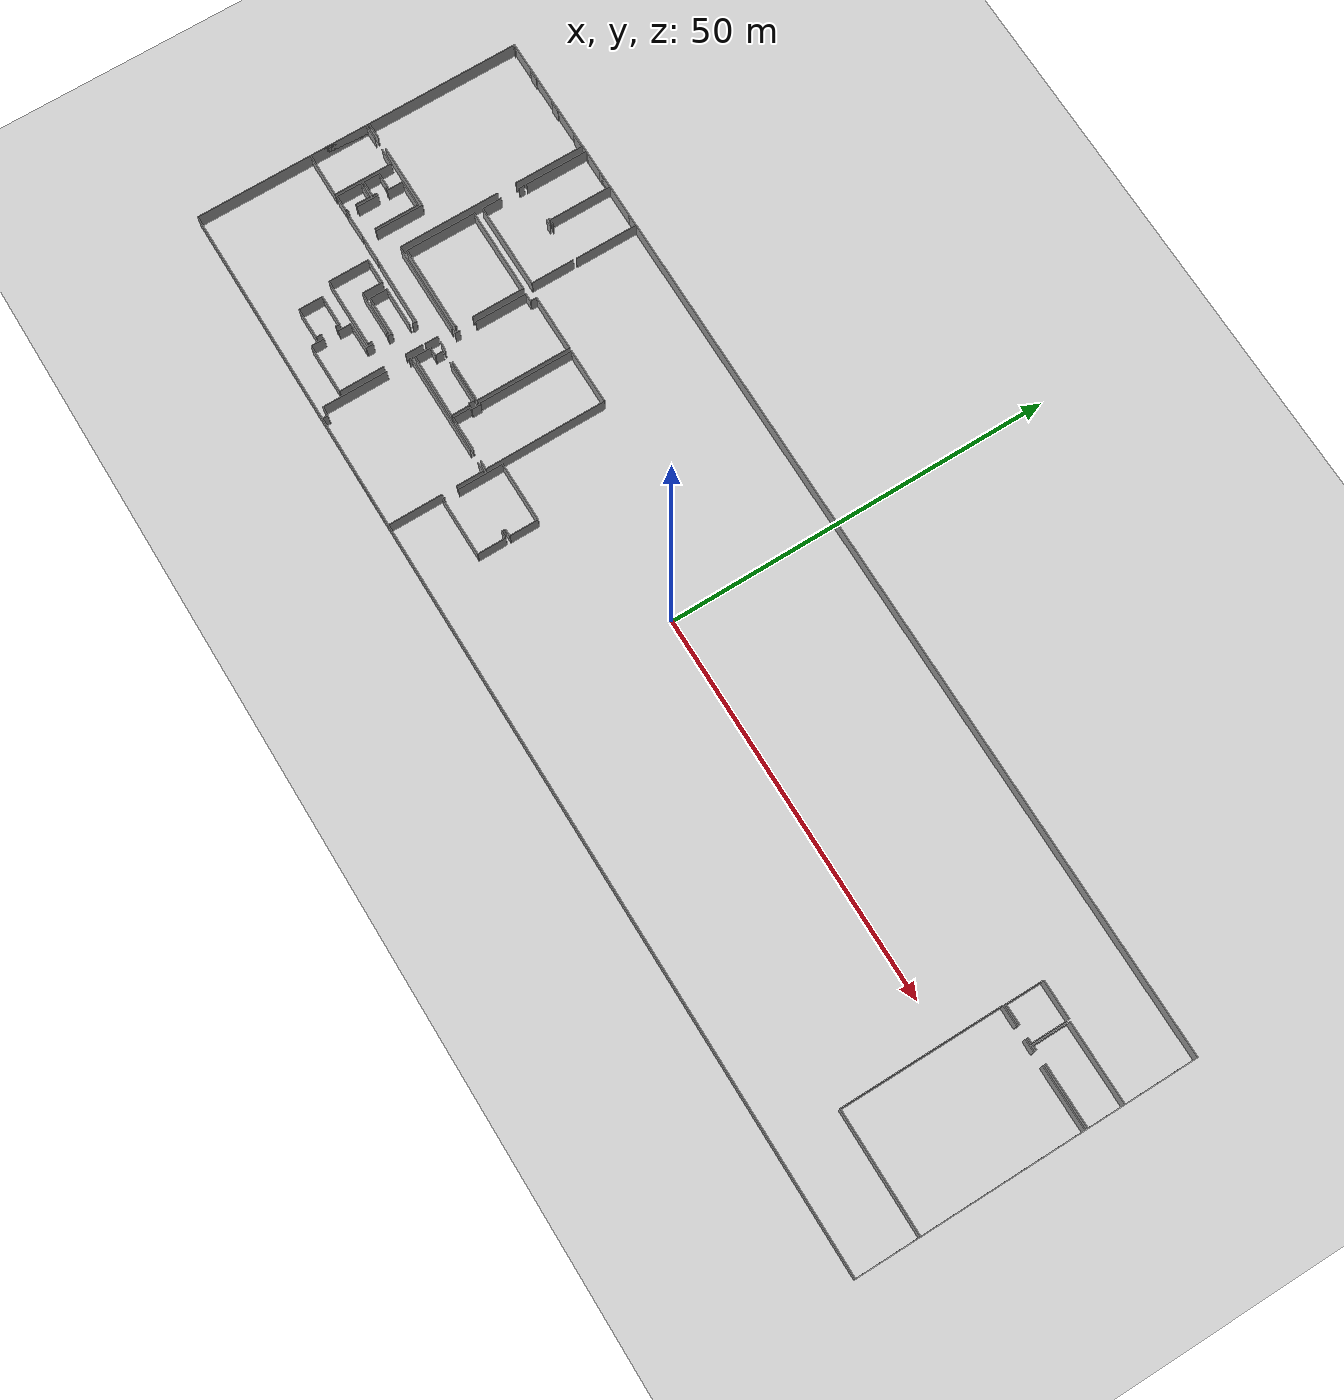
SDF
<sdf version="1.6">
  <world name="default">
    <light name="sun" type="directional">
      <cast_shadows>1</cast_shadows>
      <pose frame="">0 0 10 0 -0 0</pose>
      <diffuse>0.8 0.8 0.8 1</diffuse>
      <specular>0.1 0.1 0.1 1</specular>
      <attenuation>
        <range>1000</range>
        <constant>0.9</constant>
        <linear>0.01</linear>
        <quadratic>0.001</quadratic>
      </attenuation>
      <direction>-0.5 0.5 -1</direction>
    </light>
    <model name="ground_plane">
      <static>1</static>
      <link name="link">
        <collision name="collision">
          <geometry>
            <plane>
              <normal>0 0 1</normal>
              <size>100 100</size>
            </plane>
          </geometry>
          <surface>
            <friction>
              <ode>
                <mu>100</mu>
                <mu2>50</mu2>
              </ode>
              <torsional>
                <ode />
              </torsional>
            </friction>
            <contact>
              <ode />
            </contact>
            <bounce />
          </surface>
          <max_contacts>10</max_contacts>
        </collision>
        <visual name="visual">
          <cast_shadows>0</cast_shadows>
          <geometry>
            <plane>
              <normal>0 0 1</normal>
              <size>100 100</size>
            </plane>
          </geometry>
          <material>
            <script>
              <uri>file://media/materials/scripts/gazebo.material</uri>
              <name>Gazebo/Grey</name>
            </script>
          </material>
        </visual>
        <self_collide>0</self_collide>
        <kinematic>0</kinematic>
        <gravity>1</gravity>
      </link>
    </model>
    <gravity>0 0 -9.8</gravity>
    <magnetic_field>6e-06 2.3e-05 -4.2e-05</magnetic_field>
    <atmosphere type="adiabatic" />
    <physics default="0" name="default_physics" type="ode">
      <max_step_size>0.001</max_step_size>
      <real_time_factor>1</real_time_factor>
      <real_time_update_rate>1000</real_time_update_rate>
    </physics>
    <scene>
      <ambient>0.4 0.4 0.4 1</ambient>
      <background>0.7 0.7 0.7 1</background>
      <shadows>1</shadows>
    </scene>
    <spherical_coordinates>
      <surface_model>EARTH_WGS84</surface_model>
      <latitude_deg>0</latitude_deg>
      <longitude_deg>0</longitude_deg>
      <elevation>0</elevation>
      <heading_deg>0</heading_deg>
    </spherical_coordinates>
  <model name="0510035738_A_40_1_101">
		<static>1</static>
		<link name="Wall_0">
			<collision name="Wall_0_Collision">
				<geometry>
					<box>
						<size>19.8930888683 0.1 2.5</size>
					</box>
				</geometry>
				<pose frame="">9.94654443415 0 1.25 0 0 0</pose>
			</collision>
			<visual name="Wall_0_Visual">
				<pose frame="">9.94654443415 0 1.25 0 0 0</pose>
				<geometry>
					<box>
						<size>19.8930888683 0.1 2.5</size>
					</box>
				</geometry>
				<material>
					<script>
						<uri>file://media/materials/scripts/gazebo.material</uri>
						<name>Gazebo/Grey</name>
					</script>
					<ambient>1 1 1 1</ambient>
				</material>
			</visual>
			<pose frame="">0.00838020747362 -20.0134591211 0 0 0 1.57079632679</pose>
		</link>
		<link name="Wall_1">
			<collision name="Wall_1_Collision">
				<geometry>
					<box>
						<size>0.342318778013 0.1 2.5</size>
					</box>
				</geometry>
				<pose frame="">0.171159389007 0 1.25 0 0 0</pose>
			</collision>
			<visual name="Wall_1_Visual">
				<pose frame="">0.171159389007 0 1.25 0 0 0</pose>
				<geometry>
					<box>
						<size>0.342318778013 0.1 2.5</size>
					</box>
				</geometry>
				<material>
					<script>
						<uri>file://media/materials/scripts/gazebo.material</uri>
						<name>Gazebo/Grey</name>
					</script>
					<ambient>1 1 1 1</ambient>
				</material>
			</visual>
			<pose frame="">0.00838020747362 -0.120370252803 0 0 0 0.0</pose>
		</link>
		<link name="Wall_2">
			<collision name="Wall_2_Collision">
				<geometry>
					<box>
						<size>1.36902116637 0.1 2.5</size>
					</box>
				</geometry>
				<pose frame="">0.684510583186 0 1.25 0 0 0</pose>
			</collision>
			<visual name="Wall_2_Visual">
				<pose frame="">0.684510583186 0 1.25 0 0 0</pose>
				<geometry>
					<box>
						<size>1.36902116637 0.1 2.5</size>
					</box>
				</geometry>
				<material>
					<script>
						<uri>file://media/materials/scripts/gazebo.material</uri>
						<name>Gazebo/Grey</name>
					</script>
					<ambient>1 1 1 1</ambient>
				</material>
			</visual>
			<pose frame="">4.00751679216 -0.120370252803 0 0 0 0.0</pose>
		</link>
		<link name="Wall_3">
			<collision name="Wall_3_Collision">
				<geometry>
					<box>
						<size>1.37613164544 0.1 2.5</size>
					</box>
				</geometry>
				<pose frame="">0.688065822721 0 1.25 0 0 0</pose>
			</collision>
			<visual name="Wall_3_Visual">
				<pose frame="">0.688065822721 0 1.25 0 0 0</pose>
				<geometry>
					<box>
						<size>1.37613164544 0.1 2.5</size>
					</box>
				</geometry>
				<material>
					<script>
						<uri>file://media/materials/scripts/gazebo.material</uri>
						<name>Gazebo/Grey</name>
					</script>
					<ambient>1 1 1 1</ambient>
				</material>
			</visual>
			<pose frame="">8.96021940907 -0.120370252803 0 0 0 0.0</pose>
		</link>
		<link name="Wall_4">
			<collision name="Wall_4_Collision">
				<geometry>
					<box>
						<size>1.83069441446 0.1 2.5</size>
					</box>
				</geometry>
				<pose frame="">0.915347207232 0 1.25 0 0 0</pose>
			</collision>
			<visual name="Wall_4_Visual">
				<pose frame="">0.915347207232 0 1.25 0 0 0</pose>
				<geometry>
					<box>
						<size>1.83069441446 0.1 2.5</size>
					</box>
				</geometry>
				<material>
					<script>
						<uri>file://media/materials/scripts/gazebo.material</uri>
						<name>Gazebo/Grey</name>
					</script>
					<ambient>1 1 1 1</ambient>
				</material>
			</visual>
			<pose frame="">13.972599261 -0.120370252803 0 0 0 0.0</pose>
		</link>
		<link name="Wall_5">
			<collision name="Wall_5_Collision">
				<geometry>
					<box>
						<size>9.09633429409 0.1 2.5</size>
					</box>
				</geometry>
				<pose frame="">4.54816714705 0 1.25 0 0 0</pose>
			</collision>
			<visual name="Wall_5_Visual">
				<pose frame="">4.54816714705 0 1.25 0 0 0</pose>
				<geometry>
					<box>
						<size>9.09633429409 0.1 2.5</size>
					</box>
				</geometry>
				<material>
					<script>
						<uri>file://media/materials/scripts/gazebo.material</uri>
						<name>Gazebo/Grey</name>
					</script>
					<ambient>1 1 1 1</ambient>
				</material>
			</visual>
			<pose frame="">15.8032936755 -0.120370252803 0 0 0 -1.57079632679</pose>
		</link>
		<link name="Wall_6">
			<collision name="Wall_6_Collision">
				<geometry>
					<box>
						<size>13.2270147415 0.1 2.5</size>
					</box>
				</geometry>
				<pose frame="">6.61350737077 0 1.25 0 0 0</pose>
			</collision>
			<visual name="Wall_6_Visual">
				<pose frame="">6.61350737077 0 1.25 0 0 0</pose>
				<geometry>
					<box>
						<size>13.2270147415 0.1 2.5</size>
					</box>
				</geometry>
				<material>
					<script>
						<uri>file://media/materials/scripts/gazebo.material</uri>
						<name>Gazebo/Grey</name>
					</script>
					<ambient>1 1 1 1</ambient>
				</material>
			</visual>
			<pose frame="">15.8032936755 -11.6510278451 0 0 0 -1.57079632679</pose>
		</link>
		<link name="Wall_7">
			<collision name="Wall_7_Collision">
				<geometry>
					<box>
						<size>3.29875439643 0.1 2.5</size>
					</box>
				</geometry>
				<pose frame="">1.64937719822 0 1.25 0 0 0</pose>
			</collision>
			<visual name="Wall_7_Visual">
				<pose frame="">1.64937719822 0 1.25 0 0 0</pose>
				<geometry>
					<box>
						<size>3.29875439643 0.1 2.5</size>
					</box>
				</geometry>
				<material>
					<script>
						<uri>file://media/materials/scripts/gazebo.material</uri>
						<name>Gazebo/Grey</name>
					</script>
					<ambient>1 1 1 1</ambient>
				</material>
			</visual>
			<pose frame="">15.8032936755 -27.9271683787 0 0 0 3.14159265359</pose>
		</link>
		<link name="Wall_8">
			<collision name="Wall_8_Collision">
				<geometry>
					<box>
						<size>6.28413982249 0.1 2.5</size>
					</box>
				</geometry>
				<pose frame="">3.14206991125 0 1.25 0 0 0</pose>
			</collision>
			<visual name="Wall_8_Visual">
				<pose frame="">3.14206991125 0 1.25 0 0 0</pose>
				<geometry>
					<box>
						<size>6.28413982249 0.1 2.5</size>
					</box>
				</geometry>
				<material>
					<script>
						<uri>file://media/materials/scripts/gazebo.material</uri>
						<name>Gazebo/Grey</name>
					</script>
					<ambient>1 1 1 1</ambient>
				</material>
			</visual>
			<pose frame="">12.504539279 -26.2457940247 0 0 0 1.57079632679</pose>
		</link>
		<link name="Wall_9">
			<collision name="Wall_9_Collision">
				<geometry>
					<box>
						<size>8.73090645911 0.1 2.5</size>
					</box>
				</geometry>
				<pose frame="">4.36545322955 0 1.25 0 0 0</pose>
			</collision>
			<visual name="Wall_9_Visual">
				<pose frame="">4.36545322955 0 1.25 0 0 0</pose>
				<geometry>
					<box>
						<size>8.73090645911 0.1 2.5</size>
					</box>
				</geometry>
				<material>
					<script>
						<uri>file://media/materials/scripts/gazebo.material</uri>
						<name>Gazebo/Grey</name>
					</script>
					<ambient>1 1 1 1</ambient>
				</material>
			</visual>
			<pose frame="">12.504539279 -19.9616542022 0 0 0 3.14159265359</pose>
		</link>
		<link name="Wall_10">
			<collision name="Wall_10_Collision">
				<geometry>
					<box>
						<size>1.99617749686 0.1 2.5</size>
					</box>
				</geometry>
				<pose frame="">0.998088748432 0 1.25 0 0 0</pose>
			</collision>
			<visual name="Wall_10_Visual">
				<pose frame="">0.998088748432 0 1.25 0 0 0</pose>
				<geometry>
					<box>
						<size>1.99617749686 0.1 2.5</size>
					</box>
				</geometry>
				<material>
					<script>
						<uri>file://media/materials/scripts/gazebo.material</uri>
						<name>Gazebo/Grey</name>
					</script>
					<ambient>1 1 1 1</ambient>
				</material>
			</visual>
			<pose frame="">2.00388536892 -19.9616542022 0 0 0 -3.11563767917</pose>
		</link>
		<link name="Wall_11">
			<collision name="Wall_11_Collision">
				<geometry>
					<box>
						<size>8.20244549691 0.1 2.5</size>
					</box>
				</geometry>
				<pose frame="">4.10122274845 0 1.25 0 0 0</pose>
			</collision>
			<visual name="Wall_11_Visual">
				<pose frame="">4.10122274845 0 1.25 0 0 0</pose>
				<geometry>
					<box>
						<size>8.20244549691 0.1 2.5</size>
					</box>
				</geometry>
				<material>
					<script>
						<uri>file://media/materials/scripts/gazebo.material</uri>
						<name>Gazebo/Grey</name>
					</script>
					<ambient>1 1 1 1</ambient>
				</material>
			</visual>
			<pose frame="">16.591033178 -8.20244549691 0 0 0 1.57079632679</pose>
		</link>
		<link name="Wall_12">
			<collision name="Wall_12_Collision">
				<geometry>
					<box>
						<size>0.361110758409 0.1 2.5</size>
					</box>
				</geometry>
				<pose frame="">0.180555379204 0 1.25 0 0 0</pose>
			</collision>
			<visual name="Wall_12_Visual">
				<pose frame="">0.180555379204 0 1.25 0 0 0</pose>
				<geometry>
					<box>
						<size>0.361110758409 0.1 2.5</size>
					</box>
				</geometry>
				<material>
					<script>
						<uri>file://media/materials/scripts/gazebo.material</uri>
						<name>Gazebo/Grey</name>
					</script>
					<ambient>1 1 1 1</ambient>
				</material>
			</visual>
			<pose frame="">16.591033178 -0.0 0 0 0 0.0</pose>
		</link>
		<link name="Wall_13">
			<collision name="Wall_13_Collision">
				<geometry>
					<box>
						<size>2.37363028048 0.1 2.5</size>
					</box>
				</geometry>
				<pose frame="">1.18681514024 0 1.25 0 0 0</pose>
			</collision>
			<visual name="Wall_13_Visual">
				<pose frame="">1.18681514024 0 1.25 0 0 0</pose>
				<geometry>
					<box>
						<size>2.37363028048 0.1 2.5</size>
					</box>
				</geometry>
				<material>
					<script>
						<uri>file://media/materials/scripts/gazebo.material</uri>
						<name>Gazebo/Grey</name>
					</script>
					<ambient>1 1 1 1</ambient>
				</material>
			</visual>
			<pose frame="">19.6538720368 -0.0 0 0 0 0.0</pose>
		</link>
		<link name="Wall_14">
			<collision name="Wall_14_Collision">
				<geometry>
					<box>
						<size>8.22428482548 0.1 2.5</size>
					</box>
				</geometry>
				<pose frame="">4.11214241274 0 1.25 0 0 0</pose>
			</collision>
			<visual name="Wall_14_Visual">
				<pose frame="">4.11214241274 0 1.25 0 0 0</pose>
				<geometry>
					<box>
						<size>8.22428482548 0.1 2.5</size>
					</box>
				</geometry>
				<material>
					<script>
						<uri>file://media/materials/scripts/gazebo.material</uri>
						<name>Gazebo/Grey</name>
					</script>
					<ambient>1 1 1 1</ambient>
				</material>
			</visual>
			<pose frame="">22.0275023173 -0.0 0 0 0 -1.57079632679</pose>
		</link>
		<link name="Wall_15">
			<collision name="Wall_15_Collision">
				<geometry>
					<box>
						<size>0.217123557271 0.1 2.5</size>
					</box>
				</geometry>
				<pose frame="">0.108561778636 0 1.25 0 0 0</pose>
			</collision>
			<visual name="Wall_15_Visual">
				<pose frame="">0.108561778636 0 1.25 0 0 0</pose>
				<geometry>
					<box>
						<size>0.217123557271 0.1 2.5</size>
					</box>
				</geometry>
				<material>
					<script>
						<uri>file://media/materials/scripts/gazebo.material</uri>
						<name>Gazebo/Grey</name>
					</script>
					<ambient>1 1 1 1</ambient>
				</material>
			</visual>
			<pose frame="">22.0275023173 -8.22428482548 0 0 0 3.14159265359</pose>
		</link>
		<link name="Wall_16">
			<collision name="Wall_16_Collision">
				<geometry>
					<box>
						<size>1.52773721701 0.1 2.5</size>
					</box>
				</geometry>
				<pose frame="">0.763868608505 0 1.25 0 0 0</pose>
			</collision>
			<visual name="Wall_16_Visual">
				<pose frame="">0.763868608505 0 1.25 0 0 0</pose>
				<geometry>
					<box>
						<size>1.52773721701 0.1 2.5</size>
					</box>
				</geometry>
				<material>
					<script>
						<uri>file://media/materials/scripts/gazebo.material</uri>
						<name>Gazebo/Grey</name>
					</script>
					<ambient>1 1 1 1</ambient>
				</material>
			</visual>
			<pose frame="">26.3455946773 -0.0208235458435 0 0 0 0.0</pose>
		</link>
		<link name="Wall_17">
			<collision name="Wall_17_Collision">
				<geometry>
					<box>
						<size>8.17298779791 0.1 2.5</size>
					</box>
				</geometry>
				<pose frame="">4.08649389896 0 1.25 0 0 0</pose>
			</collision>
			<visual name="Wall_17_Visual">
				<pose frame="">4.08649389896 0 1.25 0 0 0</pose>
				<geometry>
					<box>
						<size>8.17298779791 0.1 2.5</size>
					</box>
				</geometry>
				<material>
					<script>
						<uri>file://media/materials/scripts/gazebo.material</uri>
						<name>Gazebo/Grey</name>
					</script>
					<ambient>1 1 1 1</ambient>
				</material>
			</visual>
			<pose frame="">27.8733318943 -0.0208235458435 0 0 0 -1.57079632679</pose>
		</link>
		<link name="Wall_18">
			<collision name="Wall_18_Collision">
				<geometry>
					<box>
						<size>0.291806019602 0.1 2.5</size>
					</box>
				</geometry>
				<pose frame="">0.145903009801 0 1.25 0 0 0</pose>
			</collision>
			<visual name="Wall_18_Visual">
				<pose frame="">0.145903009801 0 1.25 0 0 0</pose>
				<geometry>
					<box>
						<size>0.291806019602 0.1 2.5</size>
					</box>
				</geometry>
				<material>
					<script>
						<uri>file://media/materials/scripts/gazebo.material</uri>
						<name>Gazebo/Grey</name>
					</script>
					<ambient>1 1 1 1</ambient>
				</material>
			</visual>
			<pose frame="">22.7106161992 -8.19381134375 0 0 0 -3.09806615527</pose>
		</link>
		<link name="Wall_19">
			<collision name="Wall_19_Collision">
				<geometry>
					<box>
						<size>2.54098048427 0.1 2.5</size>
					</box>
				</geometry>
				<pose frame="">1.27049024214 0 1.25 0 0 0</pose>
			</collision>
			<visual name="Wall_19_Visual">
				<pose frame="">1.27049024214 0 1.25 0 0 0</pose>
				<geometry>
					<box>
						<size>2.54098048427 0.1 2.5</size>
					</box>
				</geometry>
				<material>
					<script>
						<uri>file://media/materials/scripts/gazebo.material</uri>
						<name>Gazebo/Grey</name>
					</script>
					<ambient>1 1 1 1</ambient>
				</material>
			</visual>
			<pose frame="">16.5834148076 -14.1772794799 0 0 0 1.57079632679</pose>
		</link>
		<link name="Wall_20">
			<collision name="Wall_20_Collision">
				<geometry>
					<box>
						<size>0.708000558681 0.1 2.5</size>
					</box>
				</geometry>
				<pose frame="">0.35400027934 0 1.25 0 0 0</pose>
			</collision>
			<visual name="Wall_20_Visual">
				<pose frame="">0.35400027934 0 1.25 0 0 0</pose>
				<geometry>
					<box>
						<size>0.708000558681 0.1 2.5</size>
					</box>
				</geometry>
				<material>
					<script>
						<uri>file://media/materials/scripts/gazebo.material</uri>
						<name>Gazebo/Grey</name>
					</script>
					<ambient>1 1 1 1</ambient>
				</material>
			</visual>
			<pose frame="">16.5834148076 -9.25174905088 0 0 0 1.57079632679</pose>
		</link>
		<link name="Wall_21">
			<collision name="Wall_21_Collision">
				<geometry>
					<box>
						<size>0.859098238887 0.1 2.5</size>
					</box>
				</geometry>
				<pose frame="">0.429549119443 0 1.25 0 0 0</pose>
			</collision>
			<visual name="Wall_21_Visual">
				<pose frame="">0.429549119443 0 1.25 0 0 0</pose>
				<geometry>
					<box>
						<size>0.859098238887 0.1 2.5</size>
					</box>
				</geometry>
				<material>
					<script>
						<uri>file://media/materials/scripts/gazebo.material</uri>
						<name>Gazebo/Grey</name>
					</script>
					<ambient>1 1 1 1</ambient>
				</material>
			</visual>
			<pose frame="">21.8228220984 -8.5437484922 0 0 0 0.0</pose>
		</link>
		<link name="Wall_22">
			<collision name="Wall_22_Collision">
				<geometry>
					<box>
						<size>5.60737458258 0.1 2.5</size>
					</box>
				</geometry>
				<pose frame="">2.80368729129 0 1.25 0 0 0</pose>
			</collision>
			<visual name="Wall_22_Visual">
				<pose frame="">2.80368729129 0 1.25 0 0 0</pose>
				<geometry>
					<box>
						<size>5.60737458258 0.1 2.5</size>
					</box>
				</geometry>
				<material>
					<script>
						<uri>file://media/materials/scripts/gazebo.material</uri>
						<name>Gazebo/Grey</name>
					</script>
					<ambient>1 1 1 1</ambient>
				</material>
			</visual>
			<pose frame="">27.8372716076 -8.5437484922 0 0 0 -1.57079632679</pose>
		</link>
		<link name="Wall_23">
			<collision name="Wall_23_Collision">
				<geometry>
					<box>
						<size>11.2538871966 0.1 2.5</size>
					</box>
				</geometry>
				<pose frame="">5.62694359829 0 1.25 0 0 0</pose>
			</collision>
			<visual name="Wall_23_Visual">
				<pose frame="">5.62694359829 0 1.25 0 0 0</pose>
				<geometry>
					<box>
						<size>11.2538871966 0.1 2.5</size>
					</box>
				</geometry>
				<material>
					<script>
						<uri>file://media/materials/scripts/gazebo.material</uri>
						<name>Gazebo/Grey</name>
					</script>
					<ambient>1 1 1 1</ambient>
				</material>
			</visual>
			<pose frame="">27.8372716076 -14.1511230748 0 0 0 -3.13926844079</pose>
		</link>
		<link name="Wall_24">
			<collision name="Wall_24_Collision">
				<geometry>
					<box>
						<size>7.58205619818 0.1 2.5</size>
					</box>
				</geometry>
				<pose frame="">3.79102809909 0 1.25 0 0 0</pose>
			</collision>
			<visual name="Wall_24_Visual">
				<pose frame="">3.79102809909 0 1.25 0 0 0</pose>
				<geometry>
					<box>
						<size>7.58205619818 0.1 2.5</size>
					</box>
				</geometry>
				<material>
					<script>
						<uri>file://media/materials/scripts/gazebo.material</uri>
						<name>Gazebo/Grey</name>
					</script>
					<ambient>1 1 1 1</ambient>
				</material>
			</visual>
			<pose frame="">0.0 -27.9596734259 0 0 0 1.57079632679</pose>
		</link>
		<link name="Wall_25">
			<collision name="Wall_25_Collision">
				<geometry>
					<box>
						<size>2.04121538403 0.1 2.5</size>
					</box>
				</geometry>
				<pose frame="">1.02060769201 0 1.25 0 0 0</pose>
			</collision>
			<visual name="Wall_25_Visual">
				<pose frame="">1.02060769201 0 1.25 0 0 0</pose>
				<geometry>
					<box>
						<size>2.04121538403 0.1 2.5</size>
					</box>
				</geometry>
				<material>
					<script>
						<uri>file://media/materials/scripts/gazebo.material</uri>
						<name>Gazebo/Grey</name>
					</script>
					<ambient>1 1 1 1</ambient>
				</material>
			</visual>
			<pose frame="">0.0 -20.3776172277 0 0 0 0.0</pose>
		</link>
		<link name="Wall_26">
			<collision name="Wall_26_Collision">
				<geometry>
					<box>
						<size>2.20678796805 0.1 2.5</size>
					</box>
				</geometry>
				<pose frame="">1.10339398403 0 1.25 0 0 0</pose>
			</collision>
			<visual name="Wall_26_Visual">
				<pose frame="">1.10339398403 0 1.25 0 0 0</pose>
				<geometry>
					<box>
						<size>2.20678796805 0.1 2.5</size>
					</box>
				</geometry>
				<material>
					<script>
						<uri>file://media/materials/scripts/gazebo.material</uri>
						<name>Gazebo/Grey</name>
					</script>
					<ambient>1 1 1 1</ambient>
				</material>
			</visual>
			<pose frame="">3.70481354038 -20.3776172277 0 0 0 0.0</pose>
		</link>
		<link name="Wall_27">
			<collision name="Wall_27_Collision">
				<geometry>
					<box>
						<size>7.61557702807 0.1 2.5</size>
					</box>
				</geometry>
				<pose frame="">3.80778851404 0 1.25 0 0 0</pose>
			</collision>
			<visual name="Wall_27_Visual">
				<pose frame="">3.80778851404 0 1.25 0 0 0</pose>
				<geometry>
					<box>
						<size>7.61557702807 0.1 2.5</size>
					</box>
				</geometry>
				<material>
					<script>
						<uri>file://media/materials/scripts/gazebo.material</uri>
						<name>Gazebo/Grey</name>
					</script>
					<ambient>1 1 1 1</ambient>
				</material>
			</visual>
			<pose frame="">5.91160150844 -20.3776172277 0 0 0 -1.57079632679</pose>
		</link>
		<link name="Wall_28">
			<collision name="Wall_28_Collision">
				<geometry>
					<box>
						<size>5.91169654504 0.1 2.5</size>
					</box>
				</geometry>
				<pose frame="">2.95584827252 0 1.25 0 0 0</pose>
			</collision>
			<visual name="Wall_28_Visual">
				<pose frame="">2.95584827252 0 1.25 0 0 0</pose>
				<geometry>
					<box>
						<size>5.91169654504 0.1 2.5</size>
					</box>
				</geometry>
				<material>
					<script>
						<uri>file://media/materials/scripts/gazebo.material</uri>
						<name>Gazebo/Grey</name>
					</script>
					<ambient>1 1 1 1</ambient>
				</material>
			</visual>
			<pose frame="">5.91160150844 -27.9931942557 0 0 0 3.1359223677</pose>
		</link>
		<link name="Wall_29">
			<collision name="Wall_29_Collision">
				<geometry>
					<box>
						<size>0.277054737992 0.1 2.5</size>
					</box>
				</geometry>
				<pose frame="">0.138527368996 0 1.25 0 0 0</pose>
			</collision>
			<visual name="Wall_29_Visual">
				<pose frame="">0.138527368996 0 1.25 0 0 0</pose>
				<geometry>
					<box>
						<size>0.277054737992 0.1 2.5</size>
					</box>
				</geometry>
				<material>
					<script>
						<uri>file://media/materials/scripts/gazebo.material</uri>
						<name>Gazebo/Grey</name>
					</script>
					<ambient>1 1 1 1</ambient>
				</material>
			</visual>
			<pose frame="">8.66742003885 -27.9642444481 0 0 0 1.57079632679</pose>
		</link>
		<link name="Wall_30">
			<collision name="Wall_30_Collision">
				<geometry>
					<box>
						<size>2.8764427289 0.1 2.5</size>
					</box>
				</geometry>
				<pose frame="">1.43822136445 0 1.25 0 0 0</pose>
			</collision>
			<visual name="Wall_30_Visual">
				<pose frame="">1.43822136445 0 1.25 0 0 0</pose>
				<geometry>
					<box>
						<size>2.8764427289 0.1 2.5</size>
					</box>
				</geometry>
				<material>
					<script>
						<uri>file://media/materials/scripts/gazebo.material</uri>
						<name>Gazebo/Grey</name>
					</script>
					<ambient>1 1 1 1</ambient>
				</material>
			</visual>
			<pose frame="">8.66742003885 -26.6152849905 0 0 0 1.57079632679</pose>
		</link>
		<link name="Wall_31">
			<collision name="Wall_31_Collision">
				<geometry>
					<box>
						<size>2.14101603667 0.1 2.5</size>
					</box>
				</geometry>
				<pose frame="">1.07050801833 0 1.25 0 0 0</pose>
			</collision>
			<visual name="Wall_31_Visual">
				<pose frame="">1.07050801833 0 1.25 0 0 0</pose>
				<geometry>
					<box>
						<size>2.14101603667 0.1 2.5</size>
					</box>
				</geometry>
				<material>
					<script>
						<uri>file://media/materials/scripts/gazebo.material</uri>
						<name>Gazebo/Grey</name>
					</script>
					<ambient>1 1 1 1</ambient>
				</material>
			</visual>
			<pose frame="">8.66742003885 -22.5437738868 0 0 0 1.57079632679</pose>
		</link>
		<link name="Wall_32">
			<collision name="Wall_32_Collision">
				<geometry>
					<box>
						<size>3.53746333659 0.1 2.5</size>
					</box>
				</geometry>
				<pose frame="">1.7687316683 0 1.25 0 0 0</pose>
			</collision>
			<visual name="Wall_32_Visual">
				<pose frame="">1.7687316683 0 1.25 0 0 0</pose>
				<geometry>
					<box>
						<size>3.53746333659 0.1 2.5</size>
					</box>
				</geometry>
				<material>
					<script>
						<uri>file://media/materials/scripts/gazebo.material</uri>
						<name>Gazebo/Grey</name>
					</script>
					<ambient>1 1 1 1</ambient>
				</material>
			</visual>
			<pose frame="">8.66742003885 -20.4027578501 0 0 0 0.0</pose>
		</link>
		<link name="Wall_33">
			<collision name="Wall_33_Collision">
				<geometry>
					<box>
						<size>5.833132293 0.1 2.5</size>
					</box>
				</geometry>
				<pose frame="">2.9165661465 0 1.25 0 0 0</pose>
			</collision>
			<visual name="Wall_33_Visual">
				<pose frame="">2.9165661465 0 1.25 0 0 0</pose>
				<geometry>
					<box>
						<size>5.833132293 0.1 2.5</size>
					</box>
				</geometry>
				<material>
					<script>
						<uri>file://media/materials/scripts/gazebo.material</uri>
						<name>Gazebo/Grey</name>
					</script>
					<ambient>1 1 1 1</ambient>
				</material>
			</visual>
			<pose frame="">12.2048833754 -20.4027578501 0 0 0 -1.57079632679</pose>
		</link>
		<link name="Wall_34">
			<collision name="Wall_34_Collision">
				<geometry>
					<box>
						<size>3.53784264876 0.1 2.5</size>
					</box>
				</geometry>
				<pose frame="">1.76892132438 0 1.25 0 0 0</pose>
			</collision>
			<visual name="Wall_34_Visual">
				<pose frame="">1.76892132438 0 1.25 0 0 0</pose>
				<geometry>
					<box>
						<size>3.53784264876 0.1 2.5</size>
					</box>
				</geometry>
				<material>
					<script>
						<uri>file://media/materials/scripts/gazebo.material</uri>
						<name>Gazebo/Grey</name>
					</script>
					<ambient>1 1 1 1</ambient>
				</material>
			</visual>
			<pose frame="">12.2048833754 -27.9124395292 0 0 0 -3.12694904855</pose>
		</link>
		<link name="Wall_35">
			<collision name="Wall_35_Collision">
				<geometry>
					<box>
						<size>3.21698388715 0.1 2.5</size>
					</box>
				</geometry>
				<pose frame="">1.60849194357 0 1.25 0 0 0</pose>
			</collision>
			<visual name="Wall_35_Visual">
				<pose frame="">1.60849194357 0 1.25 0 0 0</pose>
				<geometry>
					<box>
						<size>3.21698388715 0.1 2.5</size>
					</box>
				</geometry>
				<material>
					<script>
						<uri>file://media/materials/scripts/gazebo.material</uri>
						<name>Gazebo/Grey</name>
					</script>
					<ambient>1 1 1 1</ambient>
				</material>
			</visual>
			<pose frame="">6.24680980738 -27.9327551837 0 0 0 1.57079632679</pose>
		</link>
		<link name="Wall_36">
			<collision name="Wall_36_Collision">
				<geometry>
					<box>
						<size>2.08590982389 0.1 2.5</size>
					</box>
				</geometry>
				<pose frame="">1.04295491194 0 1.25 0 0 0</pose>
			</collision>
			<visual name="Wall_36_Visual">
				<pose frame="">1.04295491194 0 1.25 0 0 0</pose>
				<geometry>
					<box>
						<size>2.08590982389 0.1 2.5</size>
					</box>
				</geometry>
				<material>
					<script>
						<uri>file://media/materials/scripts/gazebo.material</uri>
						<name>Gazebo/Grey</name>
					</script>
					<ambient>1 1 1 1</ambient>
				</material>
			</visual>
			<pose frame="">6.24680980738 -24.7157712965 0 0 0 0.0</pose>
		</link>
		<link name="Wall_37">
			<collision name="Wall_37_Collision">
				<geometry>
					<box>
						<size>1.89951369402 0.1 2.5</size>
					</box>
				</geometry>
				<pose frame="">0.94975684701 0 1.25 0 0 0</pose>
			</collision>
			<visual name="Wall_37_Visual">
				<pose frame="">0.94975684701 0 1.25 0 0 0</pose>
				<geometry>
					<box>
						<size>1.89951369402 0.1 2.5</size>
					</box>
				</geometry>
				<material>
					<script>
						<uri>file://media/materials/scripts/gazebo.material</uri>
						<name>Gazebo/Grey</name>
					</script>
					<ambient>1 1 1 1</ambient>
				</material>
			</visual>
			<pose frame="">8.33271963127 -24.7157712965 0 0 0 -1.57079632679</pose>
		</link>
		<link name="Wall_38">
			<collision name="Wall_38_Collision">
				<geometry>
					<box>
						<size>0.219663014081 0.1 2.5</size>
					</box>
				</geometry>
				<pose frame="">0.109831507041 0 1.25 0 0 0</pose>
			</collision>
			<visual name="Wall_38_Visual">
				<pose frame="">0.109831507041 0 1.25 0 0 0</pose>
				<geometry>
					<box>
						<size>0.219663014081 0.1 2.5</size>
					</box>
				</geometry>
				<material>
					<script>
						<uri>file://media/materials/scripts/gazebo.material</uri>
						<name>Gazebo/Grey</name>
					</script>
					<ambient>1 1 1 1</ambient>
				</material>
			</visual>
			<pose frame="">8.33271963127 -27.696839646 0 0 0 -1.57079632679</pose>
		</link>
		<link name="Wall_39">
			<collision name="Wall_39_Collision">
				<geometry>
					<box>
						<size>2.08597313931 0.1 2.5</size>
					</box>
				</geometry>
				<pose frame="">1.04298656965 0 1.25 0 0 0</pose>
			</collision>
			<visual name="Wall_39_Visual">
				<pose frame="">1.04298656965 0 1.25 0 0 0</pose>
				<geometry>
					<box>
						<size>2.08597313931 0.1 2.5</size>
					</box>
				</geometry>
				<material>
					<script>
						<uri>file://media/materials/scripts/gazebo.material</uri>
						<name>Gazebo/Grey</name>
					</script>
					<ambient>1 1 1 1</ambient>
				</material>
			</visual>
			<pose frame="">8.33271963127 -27.9165026601 0 0 0 -3.1338012359</pose>
		</link>
		<link name="Wall_40">
			<collision name="Wall_40_Collision">
				<geometry>
					<box>
						<size>2.09581370545 0.1 2.5</size>
					</box>
				</geometry>
				<pose frame="">1.04790685272 0 1.25 0 0 0</pose>
			</collision>
			<visual name="Wall_40_Visual">
				<pose frame="">1.04790685272 0 1.25 0 0 0</pose>
				<geometry>
					<box>
						<size>2.09581370545 0.1 2.5</size>
					</box>
				</geometry>
				<material>
					<script>
						<uri>file://media/materials/scripts/gazebo.material</uri>
						<name>Gazebo/Grey</name>
					</script>
					<ambient>1 1 1 1</ambient>
				</material>
			</visual>
			<pose frame="">6.27093464708 -24.3546605381 0 0 0 1.57079632679</pose>
		</link>
		<link name="Wall_41">
			<collision name="Wall_41_Collision">
				<geometry>
					<box>
						<size>2.0831164214 0.1 2.5</size>
					</box>
				</geometry>
				<pose frame="">1.0415582107 0 1.25 0 0 0</pose>
			</collision>
			<visual name="Wall_41_Visual">
				<pose frame="">1.0415582107 0 1.25 0 0 0</pose>
				<geometry>
					<box>
						<size>2.0831164214 0.1 2.5</size>
					</box>
				</geometry>
				<material>
					<script>
						<uri>file://media/materials/scripts/gazebo.material</uri>
						<name>Gazebo/Grey</name>
					</script>
					<ambient>1 1 1 1</ambient>
				</material>
			</visual>
			<pose frame="">6.27093464708 -22.2588468327 0 0 0 0.0</pose>
		</link>
		<link name="Wall_42">
			<collision name="Wall_42_Collision">
				<geometry>
					<box>
						<size>0.290259913405 0.1 2.5</size>
					</box>
				</geometry>
				<pose frame="">0.145129956702 0 1.25 0 0 0</pose>
			</collision>
			<visual name="Wall_42_Visual">
				<pose frame="">0.145129956702 0 1.25 0 0 0</pose>
				<geometry>
					<box>
						<size>0.290259913405 0.1 2.5</size>
					</box>
				</geometry>
				<material>
					<script>
						<uri>file://media/materials/scripts/gazebo.material</uri>
						<name>Gazebo/Grey</name>
					</script>
					<ambient>1 1 1 1</ambient>
				</material>
			</visual>
			<pose frame="">8.35405106848 -22.2588468327 0 0 0 -1.57079632679</pose>
		</link>
		<link name="Wall_43">
			<collision name="Wall_43_Collision">
				<geometry>
					<box>
						<size>0.55588709575 0.1 2.5</size>
					</box>
				</geometry>
				<pose frame="">0.277943547875 0 1.25 0 0 0</pose>
			</collision>
			<visual name="Wall_43_Visual">
				<pose frame="">0.277943547875 0 1.25 0 0 0</pose>
				<geometry>
					<box>
						<size>0.55588709575 0.1 2.5</size>
					</box>
				</geometry>
				<material>
					<script>
						<uri>file://media/materials/scripts/gazebo.material</uri>
						<name>Gazebo/Grey</name>
					</script>
					<ambient>1 1 1 1</ambient>
				</material>
			</visual>
			<pose frame="">8.35405106848 -23.7708394174 0 0 0 -1.57079632679</pose>
		</link>
		<link name="Wall_44">
			<collision name="Wall_44_Collision">
				<geometry>
					<box>
						<size>2.08330370682 0.1 2.5</size>
					</box>
				</geometry>
				<pose frame="">1.04165185341 0 1.25 0 0 0</pose>
			</collision>
			<visual name="Wall_44_Visual">
				<pose frame="">1.04165185341 0 1.25 0 0 0</pose>
				<geometry>
					<box>
						<size>2.08330370682 0.1 2.5</size>
					</box>
				</geometry>
				<material>
					<script>
						<uri>file://media/materials/scripts/gazebo.material</uri>
						<name>Gazebo/Grey</name>
					</script>
					<ambient>1 1 1 1</ambient>
				</material>
			</visual>
			<pose frame="">8.35405106848 -24.3267265132 0 0 0 -3.12818372914</pose>
		</link>
		<link name="Wall_45">
			<collision name="Wall_45_Collision">
				<geometry>
					<box>
						<size>11.8983709385 0.1 2.5</size>
					</box>
				</geometry>
				<pose frame="">5.94918546923 0 1.25 0 0 0</pose>
			</collision>
			<visual name="Wall_45_Visual">
				<pose frame="">5.94918546923 0 1.25 0 0 0</pose>
				<geometry>
					<box>
						<size>11.8983709385 0.1 2.5</size>
					</box>
				</geometry>
				<material>
					<script>
						<uri>file://media/materials/scripts/gazebo.material</uri>
						<name>Gazebo/Grey</name>
					</script>
					<ambient>1 1 1 1</ambient>
				</material>
			</visual>
			<pose frame="">15.9957845017 -24.8925174905 0 0 0 0.0</pose>
		</link>
		<link name="Wall_46">
			<collision name="Wall_46_Collision">
				<geometry>
					<box>
						<size>0.121639981208 0.1 2.5</size>
					</box>
				</geometry>
				<pose frame="">0.060819990604 0 1.25 0 0 0</pose>
			</collision>
			<visual name="Wall_46_Visual">
				<pose frame="">0.060819990604 0 1.25 0 0 0</pose>
				<geometry>
					<box>
						<size>0.121639981208 0.1 2.5</size>
					</box>
				</geometry>
				<material>
					<script>
						<uri>file://media/materials/scripts/gazebo.material</uri>
						<name>Gazebo/Grey</name>
					</script>
					<ambient>1 1 1 1</ambient>
				</material>
			</visual>
			<pose frame="">27.8941554402 -24.8925174905 0 0 0 -1.57079632679</pose>
		</link>
		<link name="Wall_47">
			<collision name="Wall_47_Collision">
				<geometry>
					<box>
						<size>1.7900631055 0.1 2.5</size>
					</box>
				</geometry>
				<pose frame="">0.895031552751 0 1.25 0 0 0</pose>
			</collision>
			<visual name="Wall_47_Visual">
				<pose frame="">0.895031552751 0 1.25 0 0 0</pose>
				<geometry>
					<box>
						<size>1.7900631055 0.1 2.5</size>
					</box>
				</geometry>
				<material>
					<script>
						<uri>file://media/materials/scripts/gazebo.material</uri>
						<name>Gazebo/Grey</name>
					</script>
					<ambient>1 1 1 1</ambient>
				</material>
			</visual>
			<pose frame="">27.8941554402 -26.7706997473 0 0 0 -1.57079632679</pose>
		</link>
		<link name="Wall_48">
			<collision name="Wall_48_Collision">
				<geometry>
					<box>
						<size>0.587122414516 0.1 2.5</size>
					</box>
				</geometry>
				<pose frame="">0.293561207258 0 1.25 0 0 0</pose>
			</collision>
			<visual name="Wall_48_Visual">
				<pose frame="">0.293561207258 0 1.25 0 0 0</pose>
				<geometry>
					<box>
						<size>0.587122414516 0.1 2.5</size>
					</box>
				</geometry>
				<material>
					<script>
						<uri>file://media/materials/scripts/gazebo.material</uri>
						<name>Gazebo/Grey</name>
					</script>
					<ambient>1 1 1 1</ambient>
				</material>
			</visual>
			<pose frame="">24.9445763551 -28.5607628528 0 0 0 1.57079632679</pose>
		</link>
		<link name="Wall_49">
			<collision name="Wall_49_Collision">
				<geometry>
					<box>
						<size>8.94888525124 0.1 2.5</size>
					</box>
				</geometry>
				<pose frame="">4.47444262562 0 1.25 0 0 0</pose>
			</collision>
			<visual name="Wall_49_Visual">
				<pose frame="">4.47444262562 0 1.25 0 0 0</pose>
				<geometry>
					<box>
						<size>8.94888525124 0.1 2.5</size>
					</box>
				</geometry>
				<material>
					<script>
						<uri>file://media/materials/scripts/gazebo.material</uri>
						<name>Gazebo/Grey</name>
					</script>
					<ambient>1 1 1 1</ambient>
				</material>
			</visual>
			<pose frame="">24.9445763551 -27.9736404383 0 0 0 3.13702388377</pose>
		</link>
		<link name="Wall_50">
			<collision name="Wall_50_Collision">
				<geometry>
					<box>
						<size>9.08922381503 0.1 2.5</size>
					</box>
				</geometry>
				<pose frame="">4.54461190751 0 1.25 0 0 0</pose>
			</collision>
			<visual name="Wall_50_Visual">
				<pose frame="">4.54461190751 0 1.25 0 0 0</pose>
				<geometry>
					<box>
						<size>9.08922381503 0.1 2.5</size>
					</box>
				</geometry>
				<material>
					<script>
						<uri>file://media/materials/scripts/gazebo.material</uri>
						<name>Gazebo/Grey</name>
					</script>
					<ambient>1 1 1 1</ambient>
				</material>
			</visual>
			<pose frame="">16.5834148076 -24.4133219904 0 0 0 1.57079632679</pose>
		</link>
		<link name="Wall_51">
			<collision name="Wall_51_Collision">
				<geometry>
					<box>
						<size>11.2962657288 0.1 2.5</size>
					</box>
				</geometry>
				<pose frame="">5.64813286438 0 1.25 0 0 0</pose>
			</collision>
			<visual name="Wall_51_Visual">
				<pose frame="">5.64813286438 0 1.25 0 0 0</pose>
				<geometry>
					<box>
						<size>11.2962657288 0.1 2.5</size>
					</box>
				</geometry>
				<material>
					<script>
						<uri>file://media/materials/scripts/gazebo.material</uri>
						<name>Gazebo/Grey</name>
					</script>
					<ambient>1 1 1 1</ambient>
				</material>
			</visual>
			<pose frame="">16.5834148076 -15.3240981754 0 0 0 0.0</pose>
		</link>
		<link name="Wall_52">
			<collision name="Wall_52_Collision">
				<geometry>
					<box>
						<size>6.86770699747 0.1 2.5</size>
					</box>
				</geometry>
				<pose frame="">3.43385349874 0 1.25 0 0 0</pose>
			</collision>
			<visual name="Wall_52_Visual">
				<pose frame="">3.43385349874 0 1.25 0 0 0</pose>
				<geometry>
					<box>
						<size>6.86770699747 0.1 2.5</size>
					</box>
				</geometry>
				<material>
					<script>
						<uri>file://media/materials/scripts/gazebo.material</uri>
						<name>Gazebo/Grey</name>
					</script>
					<ambient>1 1 1 1</ambient>
				</material>
			</visual>
			<pose frame="">27.8796805363 -15.3240981754 0 0 0 -1.57079632679</pose>
		</link>
		<link name="Wall_53">
			<collision name="Wall_53_Collision">
				<geometry>
					<box>
						<size>0.166842312429 0.1 2.5</size>
					</box>
				</geometry>
				<pose frame="">0.0834211562147 0 1.25 0 0 0</pose>
			</collision>
			<visual name="Wall_53_Visual">
				<pose frame="">0.0834211562147 0 1.25 0 0 0</pose>
				<geometry>
					<box>
						<size>0.166842312429 0.1 2.5</size>
					</box>
				</geometry>
				<material>
					<script>
						<uri>file://media/materials/scripts/gazebo.material</uri>
						<name>Gazebo/Grey</name>
					</script>
					<ambient>1 1 1 1</ambient>
				</material>
			</visual>
			<pose frame="">27.8796805363 -24.3031095649 0 0 0 -1.57079632679</pose>
		</link>
		<link name="Wall_54">
			<collision name="Wall_54_Collision">
				<geometry>
					<box>
						<size>11.296407675 0.1 2.5</size>
					</box>
				</geometry>
				<pose frame="">5.64820383748 0 1.25 0 0 0</pose>
			</collision>
			<visual name="Wall_54_Visual">
				<pose frame="">5.64820383748 0 1.25 0 0 0</pose>
				<geometry>
					<box>
						<size>11.296407675 0.1 2.5</size>
					</box>
				</geometry>
				<material>
					<script>
						<uri>file://media/materials/scripts/gazebo.material</uri>
						<name>Gazebo/Grey</name>
					</script>
					<ambient>1 1 1 1</ambient>
				</material>
			</visual>
			<pose frame="">27.8796805363 -24.4699518773 0 0 0 3.13657954449</pose>
		</link>
		<link name="Wall_55">
			<collision name="Wall_55_Collision">
				<geometry>
					<box>
						<size>0.66787714108 0.1 2.5</size>
					</box>
				</geometry>
				<pose frame="">0.33393857054 0 1.25 0 0 0</pose>
			</collision>
			<visual name="Wall_55_Visual">
				<pose frame="">0.33393857054 0 1.25 0 0 0</pose>
				<geometry>
					<box>
						<size>0.66787714108 0.1 2.5</size>
					</box>
				</geometry>
				<material>
					<script>
						<uri>file://media/materials/scripts/gazebo.material</uri>
						<name>Gazebo/Grey</name>
					</script>
					<ambient>1 1 1 1</ambient>
				</material>
			</visual>
			<pose frame="">28.5909823889 -24.9709867059 0 0 0 1.57079632679</pose>
		</link>
		<link name="Wall_56">
			<collision name="Wall_56_Collision">
				<geometry>
					<box>
						<size>6.76231953985 0.1 2.5</size>
					</box>
				</geometry>
				<pose frame="">3.38115976993 0 1.25 0 0 0</pose>
			</collision>
			<visual name="Wall_56_Visual">
				<pose frame="">3.38115976993 0 1.25 0 0 0</pose>
				<geometry>
					<box>
						<size>6.76231953985 0.1 2.5</size>
					</box>
				</geometry>
				<material>
					<script>
						<uri>file://media/materials/scripts/gazebo.material</uri>
						<name>Gazebo/Grey</name>
					</script>
					<ambient>1 1 1 1</ambient>
				</material>
			</visual>
			<pose frame="">28.5909823889 -22.1991695976 0 0 0 1.57079632679</pose>
		</link>
		<link name="Wall_57">
			<collision name="Wall_57_Collision">
				<geometry>
					<box>
						<size>1.11355181127 0.1 2.5</size>
					</box>
				</geometry>
				<pose frame="">0.556775905634 0 1.25 0 0 0</pose>
			</collision>
			<visual name="Wall_57_Visual">
				<pose frame="">0.556775905634 0 1.25 0 0 0</pose>
				<geometry>
					<box>
						<size>1.11355181127 0.1 2.5</size>
					</box>
				</geometry>
				<material>
					<script>
						<uri>file://media/materials/scripts/gazebo.material</uri>
						<name>Gazebo/Grey</name>
					</script>
					<ambient>1 1 1 1</ambient>
				</material>
			</visual>
			<pose frame="">28.5909823889 -15.4368500578 0 0 0 0.0</pose>
		</link>
		<link name="Wall_58">
			<collision name="Wall_58_Collision">
				<geometry>
					<box>
						<size>0.818212984243 0.1 2.5</size>
					</box>
				</geometry>
				<pose frame="">0.409106492121 0 1.25 0 0 0</pose>
			</collision>
			<visual name="Wall_58_Visual">
				<pose frame="">0.409106492121 0 1.25 0 0 0</pose>
				<geometry>
					<box>
						<size>0.818212984243 0.1 2.5</size>
					</box>
				</geometry>
				<material>
					<script>
						<uri>file://media/materials/scripts/gazebo.material</uri>
						<name>Gazebo/Grey</name>
					</script>
					<ambient>1 1 1 1</ambient>
				</material>
			</visual>
			<pose frame="">29.7045342001 -15.4368500578 0 0 0 1.57079632679</pose>
		</link>
		<link name="Wall_59">
			<collision name="Wall_59_Collision">
				<geometry>
					<box>
						<size>7.3984534708 0.1 2.5</size>
					</box>
				</geometry>
				<pose frame="">3.6992267354 0 1.25 0 0 0</pose>
			</collision>
			<visual name="Wall_59_Visual">
				<pose frame="">3.6992267354 0 1.25 0 0 0</pose>
				<geometry>
					<box>
						<size>7.3984534708 0.1 2.5</size>
					</box>
				</geometry>
				<material>
					<script>
						<uri>file://media/materials/scripts/gazebo.material</uri>
						<name>Gazebo/Grey</name>
					</script>
					<ambient>1 1 1 1</ambient>
				</material>
			</visual>
			<pose frame="">29.7045342001 -14.6186370735 0 0 0 0.0</pose>
		</link>
		<link name="Wall_60">
			<collision name="Wall_60_Collision">
				<geometry>
					<box>
						<size>12.3460771741 0.1 2.5</size>
					</box>
				</geometry>
				<pose frame="">6.17303858705 0 1.25 0 0 0</pose>
			</collision>
			<visual name="Wall_60_Visual">
				<pose frame="">6.17303858705 0 1.25 0 0 0</pose>
				<geometry>
					<box>
						<size>12.3460771741 0.1 2.5</size>
					</box>
				</geometry>
				<material>
					<script>
						<uri>file://media/materials/scripts/gazebo.material</uri>
						<name>Gazebo/Grey</name>
					</script>
					<ambient>1 1 1 1</ambient>
				</material>
			</visual>
			<pose frame="">37.1029876709 -14.6186370735 0 0 0 -1.57079632679</pose>
		</link>
		<link name="Wall_61">
			<collision name="Wall_61_Collision">
				<geometry>
					<box>
						<size>5.66095712127 0.1 2.5</size>
					</box>
				</geometry>
				<pose frame="">2.83047856064 0 1.25 0 0 0</pose>
			</collision>
			<visual name="Wall_61_Visual">
				<pose frame="">2.83047856064 0 1.25 0 0 0</pose>
				<geometry>
					<box>
						<size>5.66095712127 0.1 2.5</size>
					</box>
				</geometry>
				<material>
					<script>
						<uri>file://media/materials/scripts/gazebo.material</uri>
						<name>Gazebo/Grey</name>
					</script>
					<ambient>1 1 1 1</ambient>
				</material>
			</visual>
			<pose frame="">37.1029876709 -26.9647142476 0 0 0 3.14159265359</pose>
		</link>
		<link name="Wall_62">
			<collision name="Wall_62_Collision">
				<geometry>
					<box>
						<size>1.23802246582 0.1 2.5</size>
					</box>
				</geometry>
				<pose frame="">0.619011232909 0 1.25 0 0 0</pose>
			</collision>
			<visual name="Wall_62_Visual">
				<pose frame="">0.619011232909 0 1.25 0 0 0</pose>
				<geometry>
					<box>
						<size>1.23802246582 0.1 2.5</size>
					</box>
				</geometry>
				<material>
					<script>
						<uri>file://media/materials/scripts/gazebo.material</uri>
						<name>Gazebo/Grey</name>
					</script>
					<ambient>1 1 1 1</ambient>
				</material>
			</visual>
			<pose frame="">29.8251583986 -26.9647142476 0 0 0 3.06274411815</pose>
		</link>
		<link name="Wall_63">
			<collision name="Wall_63_Collision">
				<geometry>
					<box>
						<size>2.06153103851 0.1 2.5</size>
					</box>
				</geometry>
				<pose frame="">1.03076551926 0 1.25 0 0 0</pose>
			</collision>
			<visual name="Wall_63_Visual">
				<pose frame="">1.03076551926 0 1.25 0 0 0</pose>
				<geometry>
					<box>
						<size>2.06153103851 0.1 2.5</size>
					</box>
				</geometry>
				<material>
					<script>
						<uri>file://media/materials/scripts/gazebo.material</uri>
						<name>Gazebo/Grey</name>
					</script>
					<ambient>1 1 1 1</ambient>
				</material>
			</visual>
			<pose frame="">28.6780857575 -30.3081630839 0 0 0 1.57079632679</pose>
		</link>
		<link name="Wall_64">
			<collision name="Wall_64_Collision">
				<geometry>
					<box>
						<size>1.10364792971 0.1 2.5</size>
					</box>
				</geometry>
				<pose frame="">0.551823964854 0 1.25 0 0 0</pose>
			</collision>
			<visual name="Wall_64_Visual">
				<pose frame="">0.551823964854 0 1.25 0 0 0</pose>
				<geometry>
					<box>
						<size>1.10364792971 0.1 2.5</size>
					</box>
				</geometry>
				<material>
					<script>
						<uri>file://media/materials/scripts/gazebo.material</uri>
						<name>Gazebo/Grey</name>
					</script>
					<ambient>1 1 1 1</ambient>
				</material>
			</visual>
			<pose frame="">28.6780857575 -28.2466320454 0 0 0 0.0</pose>
		</link>
		<link name="Wall_65">
			<collision name="Wall_65_Collision">
				<geometry>
					<box>
						<size>1.0020696573 0.1 2.5</size>
					</box>
				</geometry>
				<pose frame="">0.50103482865 0 1.25 0 0 0</pose>
			</collision>
			<visual name="Wall_65_Visual">
				<pose frame="">0.50103482865 0 1.25 0 0 0</pose>
				<geometry>
					<box>
						<size>1.0020696573 0.1 2.5</size>
					</box>
				</geometry>
				<material>
					<script>
						<uri>file://media/materials/scripts/gazebo.material</uri>
						<name>Gazebo/Grey</name>
					</script>
					<ambient>1 1 1 1</ambient>
				</material>
			</visual>
			<pose frame="">29.7817336872 -28.2466320454 0 0 0 1.57079632679</pose>
		</link>
		<link name="Wall_66">
			<collision name="Wall_66_Collision">
				<geometry>
					<box>
						<size>5.4933529718 0.1 2.5</size>
					</box>
				</geometry>
				<pose frame="">2.7466764859 0 1.25 0 0 0</pose>
			</collision>
			<visual name="Wall_66_Visual">
				<pose frame="">2.7466764859 0 1.25 0 0 0</pose>
				<geometry>
					<box>
						<size>5.4933529718 0.1 2.5</size>
					</box>
				</geometry>
				<material>
					<script>
						<uri>file://media/materials/scripts/gazebo.material</uri>
						<name>Gazebo/Grey</name>
					</script>
					<ambient>1 1 1 1</ambient>
				</material>
			</visual>
			<pose frame="">31.4245082977 -27.2445623881 0 0 0 0.0</pose>
		</link>
		<link name="Wall_67">
			<collision name="Wall_67_Collision">
				<geometry>
					<box>
						<size>0.781898751857 0.1 2.5</size>
					</box>
				</geometry>
				<pose frame="">0.390949375928 0 1.25 0 0 0</pose>
			</collision>
			<visual name="Wall_67_Visual">
				<pose frame="">0.390949375928 0 1.25 0 0 0</pose>
				<geometry>
					<box>
						<size>0.781898751857 0.1 2.5</size>
					</box>
				</geometry>
				<material>
					<script>
						<uri>file://media/materials/scripts/gazebo.material</uri>
						<name>Gazebo/Grey</name>
					</script>
					<ambient>1 1 1 1</ambient>
				</material>
			</visual>
			<pose frame="">36.9178612695 -27.2445623881 0 0 0 -1.57079632679</pose>
		</link>
		<link name="Wall_68">
			<collision name="Wall_68_Collision">
				<geometry>
					<box>
						<size>0.250390441485 0.1 2.5</size>
					</box>
				</geometry>
				<pose frame="">0.125195220742 0 1.25 0 0 0</pose>
			</collision>
			<visual name="Wall_68_Visual">
				<pose frame="">0.125195220742 0 1.25 0 0 0</pose>
				<geometry>
					<box>
						<size>0.250390441485 0.1 2.5</size>
					</box>
				</geometry>
				<material>
					<script>
						<uri>file://media/materials/scripts/gazebo.material</uri>
						<name>Gazebo/Grey</name>
					</script>
					<ambient>1 1 1 1</ambient>
				</material>
			</visual>
			<pose frame="">36.9178612695 -28.02646114 0 0 0 0.0</pose>
		</link>
		<link name="Wall_69">
			<collision name="Wall_69_Collision">
				<geometry>
					<box>
						<size>2.35433040873 0.1 2.5</size>
					</box>
				</geometry>
				<pose frame="">1.17716520436 0 1.25 0 0 0</pose>
			</collision>
			<visual name="Wall_69_Visual">
				<pose frame="">1.17716520436 0 1.25 0 0 0</pose>
				<geometry>
					<box>
						<size>2.35433040873 0.1 2.5</size>
					</box>
				</geometry>
				<material>
					<script>
						<uri>file://media/materials/scripts/gazebo.material</uri>
						<name>Gazebo/Grey</name>
					</script>
					<ambient>1 1 1 1</ambient>
				</material>
			</visual>
			<pose frame="">37.168251711 -28.02646114 0 0 0 -1.57079632679</pose>
		</link>
		<link name="Wall_70">
			<collision name="Wall_70_Collision">
				<geometry>
					<box>
						<size>8.4904765951 0.1 2.5</size>
					</box>
				</geometry>
				<pose frame="">4.24523829755 0 1.25 0 0 0</pose>
			</collision>
			<visual name="Wall_70_Visual">
				<pose frame="">4.24523829755 0 1.25 0 0 0</pose>
				<geometry>
					<box>
						<size>8.4904765951 0.1 2.5</size>
					</box>
				</geometry>
				<material>
					<script>
						<uri>file://media/materials/scripts/gazebo.material</uri>
						<name>Gazebo/Grey</name>
					</script>
					<ambient>1 1 1 1</ambient>
				</material>
			</visual>
			<pose frame="">37.168251711 -30.3807915487 0 0 0 3.13303843997</pose>
		</link>
		<link name="Wall_71">
			<collision name="Wall_71_Collision">
				<geometry>
					<box>
						<size>1.74562261132 0.1 2.5</size>
					</box>
				</geometry>
				<pose frame="">0.872811305662 0 1.25 0 0 0</pose>
			</collision>
			<visual name="Wall_71_Visual">
				<pose frame="">0.872811305662 0 1.25 0 0 0</pose>
				<geometry>
					<box>
						<size>1.74562261132 0.1 2.5</size>
					</box>
				</geometry>
				<material>
					<script>
						<uri>file://media/materials/scripts/gazebo.material</uri>
						<name>Gazebo/Grey</name>
					</script>
					<ambient>1 1 1 1</ambient>
				</material>
			</visual>
			<pose frame="">21.2326523357 -39.8336655789 0 0 0 1.57079632679</pose>
		</link>
		<link name="Wall_72">
			<collision name="Wall_72_Collision">
				<geometry>
					<box>
						<size>1.704483411 0.1 2.5</size>
					</box>
				</geometry>
				<pose frame="">0.852241705499 0 1.25 0 0 0</pose>
			</collision>
			<visual name="Wall_72_Visual">
				<pose frame="">0.852241705499 0 1.25 0 0 0</pose>
				<geometry>
					<box>
						<size>1.704483411 0.1 2.5</size>
					</box>
				</geometry>
				<material>
					<script>
						<uri>file://media/materials/scripts/gazebo.material</uri>
						<name>Gazebo/Grey</name>
					</script>
					<ambient>1 1 1 1</ambient>
				</material>
			</visual>
			<pose frame="">21.2326523357 -36.273347131 0 0 0 1.57079632679</pose>
		</link>
		<link name="Wall_73">
			<collision name="Wall_73_Collision">
				<geometry>
					<box>
						<size>3.54736721815 0.1 2.5</size>
					</box>
				</geometry>
				<pose frame="">1.77368360908 0 1.25 0 0 0</pose>
			</collision>
			<visual name="Wall_73_Visual">
				<pose frame="">1.77368360908 0 1.25 0 0 0</pose>
				<geometry>
					<box>
						<size>3.54736721815 0.1 2.5</size>
					</box>
				</geometry>
				<material>
					<script>
						<uri>file://media/materials/scripts/gazebo.material</uri>
						<name>Gazebo/Grey</name>
					</script>
					<ambient>1 1 1 1</ambient>
				</material>
			</visual>
			<pose frame="">21.2326523357 -34.5688637201 0 0 0 0.0</pose>
		</link>
		<link name="Wall_74">
			<collision name="Wall_74_Collision">
				<geometry>
					<box>
						<size>0.95966072857 0.1 2.5</size>
					</box>
				</geometry>
				<pose frame="">0.479830364285 0 1.25 0 0 0</pose>
			</collision>
			<visual name="Wall_74_Visual">
				<pose frame="">0.479830364285 0 1.25 0 0 0</pose>
				<geometry>
					<box>
						<size>0.95966072857 0.1 2.5</size>
					</box>
				</geometry>
				<material>
					<script>
						<uri>file://media/materials/scripts/gazebo.material</uri>
						<name>Gazebo/Grey</name>
					</script>
					<ambient>1 1 1 1</ambient>
				</material>
			</visual>
			<pose frame="">24.7800195538 -34.5688637201 0 0 0 1.57079632679</pose>
		</link>
		<link name="Wall_75">
			<collision name="Wall_75_Collision">
				<geometry>
					<box>
						<size>0.592963165179 0.1 2.5</size>
					</box>
				</geometry>
				<pose frame="">0.296481582589 0 1.25 0 0 0</pose>
			</collision>
			<visual name="Wall_75_Visual">
				<pose frame="">0.296481582589 0 1.25 0 0 0</pose>
				<geometry>
					<box>
						<size>0.592963165179 0.1 2.5</size>
					</box>
				</geometry>
				<material>
					<script>
						<uri>file://media/materials/scripts/gazebo.material</uri>
						<name>Gazebo/Grey</name>
					</script>
					<ambient>1 1 1 1</ambient>
				</material>
			</visual>
			<pose frame="">24.7800195538 -31.7094353518 0 0 0 1.57079632679</pose>
		</link>
		<link name="Wall_76">
			<collision name="Wall_76_Collision">
				<geometry>
					<box>
						<size>5.17719059893 0.1 2.5</size>
					</box>
				</geometry>
				<pose frame="">2.58859529947 0 1.25 0 0 0</pose>
			</collision>
			<visual name="Wall_76_Visual">
				<pose frame="">2.58859529947 0 1.25 0 0 0</pose>
				<geometry>
					<box>
						<size>5.17719059893 0.1 2.5</size>
					</box>
				</geometry>
				<material>
					<script>
						<uri>file://media/materials/scripts/gazebo.material</uri>
						<name>Gazebo/Grey</name>
					</script>
					<ambient>1 1 1 1</ambient>
				</material>
			</visual>
			<pose frame="">24.7800195538 -31.1164721866 0 0 0 3.14159265359</pose>
		</link>
		<link name="Wall_77">
			<collision name="Wall_77_Collision">
				<geometry>
					<box>
						<size>2.27179806239 0.1 2.5</size>
					</box>
				</geometry>
				<pose frame="">1.1358990312 0 1.25 0 0 0</pose>
			</collision>
			<visual name="Wall_77_Visual">
				<pose frame="">1.1358990312 0 1.25 0 0 0</pose>
				<geometry>
					<box>
						<size>2.27179806239 0.1 2.5</size>
					</box>
				</geometry>
				<material>
					<script>
						<uri>file://media/materials/scripts/gazebo.material</uri>
						<name>Gazebo/Grey</name>
					</script>
					<ambient>1 1 1 1</ambient>
				</material>
			</visual>
			<pose frame="">19.6028289549 -31.1164721866 0 0 0 1.57079632679</pose>
		</link>
		<link name="Wall_78">
			<collision name="Wall_78_Collision">
				<geometry>
					<box>
						<size>5.30975024442 0.1 2.5</size>
					</box>
				</geometry>
				<pose frame="">2.65487512221 0 1.25 0 0 0</pose>
			</collision>
			<visual name="Wall_78_Visual">
				<pose frame="">2.65487512221 0 1.25 0 0 0</pose>
				<geometry>
					<box>
						<size>5.30975024442 0.1 2.5</size>
					</box>
				</geometry>
				<material>
					<script>
						<uri>file://media/materials/scripts/gazebo.material</uri>
						<name>Gazebo/Grey</name>
					</script>
					<ambient>1 1 1 1</ambient>
				</material>
			</visual>
			<pose frame="">19.6028289549 -28.8446741242 0 0 0 0.0</pose>
		</link>
		<link name="Wall_79">
			<collision name="Wall_79_Collision">
				<geometry>
					<box>
						<size>2.28982820575 0.1 2.5</size>
					</box>
				</geometry>
				<pose frame="">1.14491410287 0 1.25 0 0 0</pose>
			</collision>
			<visual name="Wall_79_Visual">
				<pose frame="">1.14491410287 0 1.25 0 0 0</pose>
				<geometry>
					<box>
						<size>2.28982820575 0.1 2.5</size>
					</box>
				</geometry>
				<material>
					<script>
						<uri>file://media/materials/scripts/gazebo.material</uri>
						<name>Gazebo/Grey</name>
					</script>
					<ambient>1 1 1 1</ambient>
				</material>
			</visual>
			<pose frame="">27.8606346103 -28.8446741242 0 0 0 -1.57079632679</pose>
		</link>
		<link name="Wall_80">
			<collision name="Wall_80_Collision">
				<geometry>
					<box>
						<size>5.83084678187 0.1 2.5</size>
					</box>
				</geometry>
				<pose frame="">2.91542339094 0 1.25 0 0 0</pose>
			</collision>
			<visual name="Wall_80_Visual">
				<pose frame="">2.91542339094 0 1.25 0 0 0</pose>
				<geometry>
					<box>
						<size>5.83084678187 0.1 2.5</size>
					</box>
				</geometry>
				<material>
					<script>
						<uri>file://media/materials/scripts/gazebo.material</uri>
						<name>Gazebo/Grey</name>
					</script>
					<ambient>1 1 1 1</ambient>
				</material>
			</visual>
			<pose frame="">27.8606346103 -33.9672664017 0 0 0 -1.57079632679</pose>
		</link>
		<link name="Wall_81">
			<collision name="Wall_81_Collision">
				<geometry>
					<box>
						<size>6.62807762516 0.1 2.5</size>
					</box>
				</geometry>
				<pose frame="">3.31403881258 0 1.25 0 0 0</pose>
			</collision>
			<visual name="Wall_81_Visual">
				<pose frame="">3.31403881258 0 1.25 0 0 0</pose>
				<geometry>
					<box>
						<size>6.62807762516 0.1 2.5</size>
					</box>
				</geometry>
				<material>
					<script>
						<uri>file://media/materials/scripts/gazebo.material</uri>
						<name>Gazebo/Grey</name>
					</script>
					<ambient>1 1 1 1</ambient>
				</material>
			</visual>
			<pose frame="">27.8606346103 -39.7981131836 0 0 0 -3.13622872036</pose>
		</link>
		<link name="Wall_82">
			<collision name="Wall_82_Collision">
				<geometry>
					<box>
						<size>5.23966123646 0.1 2.5</size>
					</box>
				</geometry>
				<pose frame="">2.61983061823 0 1.25 0 0 0</pose>
			</collision>
			<visual name="Wall_82_Visual">
				<pose frame="">2.61983061823 0 1.25 0 0 0</pose>
				<geometry>
					<box>
						<size>5.23966123646 0.1 2.5</size>
					</box>
				</geometry>
				<material>
					<script>
						<uri>file://media/materials/scripts/gazebo.material</uri>
						<name>Gazebo/Grey</name>
					</script>
					<ambient>1 1 1 1</ambient>
				</material>
			</visual>
			<pose frame="">15.2603578095 -34.101603667 0 0 0 1.57079632679</pose>
		</link>
		<link name="Wall_83">
			<collision name="Wall_83_Collision">
				<geometry>
					<box>
						<size>3.33303706337 0.1 2.5</size>
					</box>
				</geometry>
				<pose frame="">1.66651853169 0 1.25 0 0 0</pose>
			</collision>
			<visual name="Wall_83_Visual">
				<pose frame="">1.66651853169 0 1.25 0 0 0</pose>
				<geometry>
					<box>
						<size>3.33303706337 0.1 2.5</size>
					</box>
				</geometry>
				<material>
					<script>
						<uri>file://media/materials/scripts/gazebo.material</uri>
						<name>Gazebo/Grey</name>
					</script>
					<ambient>1 1 1 1</ambient>
				</material>
			</visual>
			<pose frame="">15.2603578095 -28.8619424305 0 0 0 0.0</pose>
		</link>
		<link name="Wall_84">
			<collision name="Wall_84_Collision">
				<geometry>
					<box>
						<size>2.66414413957 0.1 2.5</size>
					</box>
				</geometry>
				<pose frame="">1.33207206978 0 1.25 0 0 0</pose>
			</collision>
			<visual name="Wall_84_Visual">
				<pose frame="">1.33207206978 0 1.25 0 0 0</pose>
				<geometry>
					<box>
						<size>2.66414413957 0.1 2.5</size>
					</box>
				</geometry>
				<material>
					<script>
						<uri>file://media/materials/scripts/gazebo.material</uri>
						<name>Gazebo/Grey</name>
					</script>
					<ambient>1 1 1 1</ambient>
				</material>
			</visual>
			<pose frame="">18.5933948728 -28.8619424305 0 0 0 -1.57079632679</pose>
		</link>
		<link name="Wall_85">
			<collision name="Wall_85_Collision">
				<geometry>
					<box>
						<size>5.833132293 0.1 2.5</size>
					</box>
				</geometry>
				<pose frame="">2.9165661465 0 1.25 0 0 0</pose>
			</collision>
			<visual name="Wall_85_Visual">
				<pose frame="">2.9165661465 0 1.25 0 0 0</pose>
				<geometry>
					<box>
						<size>5.833132293 0.1 2.5</size>
					</box>
				</geometry>
				<material>
					<script>
						<uri>file://media/materials/scripts/gazebo.material</uri>
						<name>Gazebo/Grey</name>
					</script>
					<ambient>1 1 1 1</ambient>
				</material>
			</visual>
			<pose frame="">18.5933948728 -31.5260865701 0 0 0 0.0</pose>
		</link>
		<link name="Wall_86">
			<collision name="Wall_86_Collision">
				<geometry>
					<box>
						<size>0.189189532359 0.1 2.5</size>
					</box>
				</geometry>
				<pose frame="">0.0945947661795 0 1.25 0 0 0</pose>
			</collision>
			<visual name="Wall_86_Visual">
				<pose frame="">0.0945947661795 0 1.25 0 0 0</pose>
				<geometry>
					<box>
						<size>0.189189532359 0.1 2.5</size>
					</box>
				</geometry>
				<material>
					<script>
						<uri>file://media/materials/scripts/gazebo.material</uri>
						<name>Gazebo/Grey</name>
					</script>
					<ambient>1 1 1 1</ambient>
				</material>
			</visual>
			<pose frame="">24.4265271658 -31.5260865701 0 0 0 -1.57079632679</pose>
		</link>
		<link name="Wall_87">
			<collision name="Wall_87_Collision">
				<geometry>
					<box>
						<size>0.483004685298 0.1 2.5</size>
					</box>
				</geometry>
				<pose frame="">0.241502342649 0 1.25 0 0 0</pose>
			</collision>
			<visual name="Wall_87_Visual">
				<pose frame="">0.241502342649 0 1.25 0 0 0</pose>
				<geometry>
					<box>
						<size>0.483004685298 0.1 2.5</size>
					</box>
				</geometry>
				<material>
					<script>
						<uri>file://media/materials/scripts/gazebo.material</uri>
						<name>Gazebo/Grey</name>
					</script>
					<ambient>1 1 1 1</ambient>
				</material>
			</visual>
			<pose frame="">24.4265271658 -33.6086951001 0 0 0 -1.57079632679</pose>
		</link>
		<link name="Wall_88">
			<collision name="Wall_88_Collision">
				<geometry>
					<box>
						<size>9.16617470686 0.1 2.5</size>
					</box>
				</geometry>
				<pose frame="">4.58308735343 0 1.25 0 0 0</pose>
			</collision>
			<visual name="Wall_88_Visual">
				<pose frame="">4.58308735343 0 1.25 0 0 0</pose>
				<geometry>
					<box>
						<size>9.16617470686 0.1 2.5</size>
					</box>
				</geometry>
				<material>
					<script>
						<uri>file://media/materials/scripts/gazebo.material</uri>
						<name>Gazebo/Grey</name>
					</script>
					<ambient>1 1 1 1</ambient>
				</material>
			</visual>
			<pose frame="">24.4265271658 -34.0916997854 0 0 0 -3.14051217195</pose>
		</link>
		<link name="Wall_89">
			<collision name="Wall_89_Collision">
				<geometry>
					<box>
						<size>3.12175425676 0.1 2.5</size>
					</box>
				</geometry>
				<pose frame="">1.56087712838 0 1.25 0 0 0</pose>
			</collision>
			<visual name="Wall_89_Visual">
				<pose frame="">1.56087712838 0 1.25 0 0 0</pose>
				<geometry>
					<box>
						<size>3.12175425676 0.1 2.5</size>
					</box>
				</geometry>
				<material>
					<script>
						<uri>file://media/materials/scripts/gazebo.material</uri>
						<name>Gazebo/Grey</name>
					</script>
					<ambient>1 1 1 1</ambient>
				</material>
			</visual>
			<pose frame="">16.5252612466 -38.8021382226 0 0 0 1.57079632679</pose>
		</link>
		<link name="Wall_90">
			<collision name="Wall_90_Collision">
				<geometry>
					<box>
						<size>4.08014525693 0.1 2.5</size>
					</box>
				</geometry>
				<pose frame="">2.04007262846 0 1.25 0 0 0</pose>
			</collision>
			<visual name="Wall_90_Visual">
				<pose frame="">2.04007262846 0 1.25 0 0 0</pose>
				<geometry>
					<box>
						<size>4.08014525693 0.1 2.5</size>
					</box>
				</geometry>
				<material>
					<script>
						<uri>file://media/materials/scripts/gazebo.material</uri>
						<name>Gazebo/Grey</name>
					</script>
					<ambient>1 1 1 1</ambient>
				</material>
			</visual>
			<pose frame="">16.5252612466 -35.6803839659 0 0 0 0.0</pose>
		</link>
		<link name="Wall_91">
			<collision name="Wall_91_Collision">
				<geometry>
					<box>
						<size>0.574171184784 0.1 2.5</size>
					</box>
				</geometry>
				<pose frame="">0.287085592392 0 1.25 0 0 0</pose>
			</collision>
			<visual name="Wall_91_Visual">
				<pose frame="">0.287085592392 0 1.25 0 0 0</pose>
				<geometry>
					<box>
						<size>0.574171184784 0.1 2.5</size>
					</box>
				</geometry>
				<material>
					<script>
						<uri>file://media/materials/scripts/gazebo.material</uri>
						<name>Gazebo/Grey</name>
					</script>
					<ambient>1 1 1 1</ambient>
				</material>
			</visual>
			<pose frame="">20.6054065035 -35.6803839659 0 0 0 -1.57079632679</pose>
		</link>
		<link name="Wall_92">
			<collision name="Wall_92_Collision">
				<geometry>
					<box>
						<size>0.697080894397 0.1 2.5</size>
					</box>
				</geometry>
				<pose frame="">0.348540447198 0 1.25 0 0 0</pose>
			</collision>
			<visual name="Wall_92_Visual">
				<pose frame="">0.348540447198 0 1.25 0 0 0</pose>
				<geometry>
					<box>
						<size>0.697080894397 0.1 2.5</size>
					</box>
				</geometry>
				<material>
					<script>
						<uri>file://media/materials/scripts/gazebo.material</uri>
						<name>Gazebo/Grey</name>
					</script>
					<ambient>1 1 1 1</ambient>
				</material>
			</visual>
			<pose frame="">20.6054065035 -38.0740759552 0 0 0 -1.57079632679</pose>
		</link>
		<link name="Wall_93">
			<collision name="Wall_93_Collision">
				<geometry>
					<box>
						<size>4.08026287917 0.1 2.5</size>
					</box>
				</geometry>
				<pose frame="">2.04013143958 0 1.25 0 0 0</pose>
			</collision>
			<visual name="Wall_93_Visual">
				<pose frame="">2.04013143958 0 1.25 0 0 0</pose>
				<geometry>
					<box>
						<size>4.08026287917 0.1 2.5</size>
					</box>
				</geometry>
				<material>
					<script>
						<uri>file://media/materials/scripts/gazebo.material</uri>
						<name>Gazebo/Grey</name>
					</script>
					<ambient>1 1 1 1</ambient>
				</material>
			</visual>
			<pose frame="">20.6054065035 -38.7711568495 0 0 0 -3.13399959606</pose>
		</link>
		<link name="Wall_94">
			<collision name="Wall_94_Collision">
				<geometry>
					<box>
						<size>8.39874550834 0.1 2.5</size>
					</box>
				</geometry>
				<pose frame="">4.19937275417 0 1.25 0 0 0</pose>
			</collision>
			<visual name="Wall_94_Visual">
				<pose frame="">4.19937275417 0 1.25 0 0 0</pose>
				<geometry>
					<box>
						<size>8.39874550834 0.1 2.5</size>
					</box>
				</geometry>
				<material>
					<script>
						<uri>file://media/materials/scripts/gazebo.material</uri>
						<name>Gazebo/Grey</name>
					</script>
					<ambient>1 1 1 1</ambient>
				</material>
			</visual>
			<pose frame="">28.5358761761 -42.3863275645 0 0 0 1.57079632679</pose>
		</link>
		<link name="Wall_95">
			<collision name="Wall_95_Collision">
				<geometry>
					<box>
						<size>0.345620071867 0.1 2.5</size>
					</box>
				</geometry>
				<pose frame="">0.172810035933 0 1.25 0 0 0</pose>
			</collision>
			<visual name="Wall_95_Visual">
				<pose frame="">0.172810035933 0 1.25 0 0 0</pose>
				<geometry>
					<box>
						<size>0.345620071867 0.1 2.5</size>
					</box>
				</geometry>
				<material>
					<script>
						<uri>file://media/materials/scripts/gazebo.material</uri>
						<name>Gazebo/Grey</name>
					</script>
					<ambient>1 1 1 1</ambient>
				</material>
			</visual>
			<pose frame="">28.5358761761 -31.0738093122 0 0 0 1.57079632679</pose>
		</link>
		<link name="Wall_96">
			<collision name="Wall_96_Collision">
				<geometry>
					<box>
						<size>13.465469736 0.1 2.5</size>
					</box>
				</geometry>
				<pose frame="">6.73273486801 0 1.25 0 0 0</pose>
			</collision>
			<visual name="Wall_96_Visual">
				<pose frame="">6.73273486801 0 1.25 0 0 0</pose>
				<geometry>
					<box>
						<size>13.465469736 0.1 2.5</size>
					</box>
				</geometry>
				<material>
					<script>
						<uri>file://media/materials/scripts/gazebo.material</uri>
						<name>Gazebo/Grey</name>
					</script>
					<ambient>1 1 1 1</ambient>
				</material>
			</visual>
			<pose frame="">28.5358761761 -30.7281892403 0 0 0 0.0</pose>
		</link>
		<link name="Wall_97">
			<collision name="Wall_97_Collision">
				<geometry>
					<box>
						<size>1.20954327869 0.1 2.5</size>
					</box>
				</geometry>
				<pose frame="">0.604771639346 0 1.25 0 0 0</pose>
			</collision>
			<visual name="Wall_97_Visual">
				<pose frame="">0.604771639346 0 1.25 0 0 0</pose>
				<geometry>
					<box>
						<size>1.20954327869 0.1 2.5</size>
					</box>
				</geometry>
				<material>
					<script>
						<uri>file://media/materials/scripts/gazebo.material</uri>
						<name>Gazebo/Grey</name>
					</script>
					<ambient>1 1 1 1</ambient>
				</material>
			</visual>
			<pose frame="">43.6545322955 -30.7281892403 0 0 0 0.0</pose>
		</link>
		<link name="Wall_98">
			<collision name="Wall_98_Collision">
				<geometry>
					<box>
						<size>3.53314626001 0.1 2.5</size>
					</box>
				</geometry>
				<pose frame="">1.76657313001 0 1.25 0 0 0</pose>
			</collision>
			<visual name="Wall_98_Visual">
				<pose frame="">1.76657313001 0 1.25 0 0 0</pose>
				<geometry>
					<box>
						<size>3.53314626001 0.1 2.5</size>
					</box>
				</geometry>
				<material>
					<script>
						<uri>file://media/materials/scripts/gazebo.material</uri>
						<name>Gazebo/Grey</name>
					</script>
					<ambient>1 1 1 1</ambient>
				</material>
			</visual>
			<pose frame="">44.8640755742 -30.7281892403 0 0 0 -1.57079632679</pose>
		</link>
		<link name="Wall_99">
			<collision name="Wall_99_Collision">
				<geometry>
					<box>
						<size>7.04039006057 0.1 2.5</size>
					</box>
				</geometry>
				<pose frame="">3.52019503028 0 1.25 0 0 0</pose>
			</collision>
			<visual name="Wall_99_Visual">
				<pose frame="">3.52019503028 0 1.25 0 0 0</pose>
				<geometry>
					<box>
						<size>7.04039006057 0.1 2.5</size>
					</box>
				</geometry>
				<material>
					<script>
						<uri>file://media/materials/scripts/gazebo.material</uri>
						<name>Gazebo/Grey</name>
					</script>
					<ambient>1 1 1 1</ambient>
				</material>
			</visual>
			<pose frame="">44.8640755742 -36.0854273271 0 0 0 -1.57079632679</pose>
		</link>
		<link name="Wall_100">
			<collision name="Wall_100_Collision">
				<geometry>
					<box>
						<size>15.1090061836 0.1 2.5</size>
					</box>
				</geometry>
				<pose frame="">7.55450309179 0 1.25 0 0 0</pose>
			</collision>
			<visual name="Wall_100_Visual">
				<pose frame="">7.55450309179 0 1.25 0 0 0</pose>
				<geometry>
					<box>
						<size>15.1090061836 0.1 2.5</size>
					</box>
				</geometry>
				<material>
					<script>
						<uri>file://media/materials/scripts/gazebo.material</uri>
						<name>Gazebo/Grey</name>
					</script>
					<ambient>1 1 1 1</ambient>
				</material>
			</visual>
			<pose frame="">44.8640755742 -43.1258173877 0 0 0 3.14159265359</pose>
		</link>
		<link name="Wall_101">
			<collision name="Wall_101_Collision">
				<geometry>
					<box>
						<size>0.706476884594 0.1 2.5</size>
					</box>
				</geometry>
				<pose frame="">0.353238442297 0 1.25 0 0 0</pose>
			</collision>
			<visual name="Wall_101_Visual">
				<pose frame="">0.353238442297 0 1.25 0 0 0</pose>
				<geometry>
					<box>
						<size>0.706476884594 0.1 2.5</size>
					</box>
				</geometry>
				<material>
					<script>
						<uri>file://media/materials/scripts/gazebo.material</uri>
						<name>Gazebo/Grey</name>
					</script>
					<ambient>1 1 1 1</ambient>
				</material>
			</visual>
			<pose frame="">29.7550693907 -43.1258173877 0 0 0 1.57079632679</pose>
		</link>
		<link name="Wall_102">
			<collision name="Wall_102_Collision">
				<geometry>
					<box>
						<size>1.21964008977 0.1 2.5</size>
					</box>
				</geometry>
				<pose frame="">0.609820044884 0 1.25 0 0 0</pose>
			</collision>
			<visual name="Wall_102_Visual">
				<pose frame="">0.609820044884 0 1.25 0 0 0</pose>
				<geometry>
					<box>
						<size>1.21964008977 0.1 2.5</size>
					</box>
				</geometry>
				<material>
					<script>
						<uri>file://media/materials/scripts/gazebo.material</uri>
						<name>Gazebo/Grey</name>
					</script>
					<ambient>1 1 1 1</ambient>
				</material>
			</visual>
			<pose frame="">29.7550693907 -42.4193405031 0 0 0 3.11452157633</pose>
		</link>
		<link name="Wall_103">
			<collision name="Wall_103_Collision">
				<geometry>
					<box>
						<size>2.29744657618 0.1 2.5</size>
					</box>
				</geometry>
				<pose frame="">1.14872328809 0 1.25 0 0 0</pose>
			</collision>
			<visual name="Wall_103_Visual">
				<pose frame="">1.14872328809 0 1.25 0 0 0</pose>
				<geometry>
					<box>
						<size>2.29744657618 0.1 2.5</size>
					</box>
				</geometry>
				<material>
					<script>
						<uri>file://media/materials/scripts/gazebo.material</uri>
						<name>Gazebo/Grey</name>
					</script>
					<ambient>1 1 1 1</ambient>
				</material>
			</visual>
			<pose frame="">37.5059994667 -30.3843467882 0 0 0 1.57079632679</pose>
		</link>
		<link name="Wall_104">
			<collision name="Wall_104_Collision">
				<geometry>
					<box>
						<size>0.232360298132 0.1 2.5</size>
					</box>
				</geometry>
				<pose frame="">0.116180149066 0 1.25 0 0 0</pose>
			</collision>
			<visual name="Wall_104_Visual">
				<pose frame="">0.116180149066 0 1.25 0 0 0</pose>
				<geometry>
					<box>
						<size>0.232360298132 0.1 2.5</size>
					</box>
				</geometry>
				<material>
					<script>
						<uri>file://media/materials/scripts/gazebo.material</uri>
						<name>Gazebo/Grey</name>
					</script>
					<ambient>1 1 1 1</ambient>
				</material>
			</visual>
			<pose frame="">37.5059994667 -28.086900212 0 0 0 0.0</pose>
		</link>
		<link name="Wall_105">
			<collision name="Wall_105_Collision">
				<geometry>
					<box>
						<size>1.1907512983 0.1 2.5</size>
					</box>
				</geometry>
				<pose frame="">0.595375649149 0 1.25 0 0 0</pose>
			</collision>
			<visual name="Wall_105_Visual">
				<pose frame="">0.595375649149 0 1.25 0 0 0</pose>
				<geometry>
					<box>
						<size>1.1907512983 0.1 2.5</size>
					</box>
				</geometry>
				<material>
					<script>
						<uri>file://media/materials/scripts/gazebo.material</uri>
						<name>Gazebo/Grey</name>
					</script>
					<ambient>1 1 1 1</ambient>
				</material>
			</visual>
			<pose frame="">37.7383597648 -28.086900212 0 0 0 1.57079632679</pose>
		</link>
		<link name="Wall_106">
			<collision name="Wall_106_Collision">
				<geometry>
					<box>
						<size>0.203410490496 0.1 2.5</size>
					</box>
				</geometry>
				<pose frame="">0.101705245248 0 1.25 0 0 0</pose>
			</collision>
			<visual name="Wall_106_Visual">
				<pose frame="">0.101705245248 0 1.25 0 0 0</pose>
				<geometry>
					<box>
						<size>0.203410490496 0.1 2.5</size>
					</box>
				</geometry>
				<material>
					<script>
						<uri>file://media/materials/scripts/gazebo.material</uri>
						<name>Gazebo/Grey</name>
					</script>
					<ambient>1 1 1 1</ambient>
				</material>
			</visual>
			<pose frame="">37.7383597648 -26.8961489137 0 0 0 3.14159265359</pose>
		</link>
		<link name="Wall_107">
			<collision name="Wall_107_Collision">
				<geometry>
					<box>
						<size>12.2632908821 0.1 2.5</size>
					</box>
				</geometry>
				<pose frame="">6.13164544104 0 1.25 0 0 0</pose>
			</collision>
			<visual name="Wall_107_Visual">
				<pose frame="">6.13164544104 0 1.25 0 0 0</pose>
				<geometry>
					<box>
						<size>12.2632908821 0.1 2.5</size>
					</box>
				</geometry>
				<material>
					<script>
						<uri>file://media/materials/scripts/gazebo.material</uri>
						<name>Gazebo/Grey</name>
					</script>
					<ambient>1 1 1 1</ambient>
				</material>
			</visual>
			<pose frame="">37.5349492744 -26.8961489137 0 0 0 1.57079632679</pose>
		</link>
		<link name="Wall_108">
			<collision name="Wall_108_Collision">
				<geometry>
					<box>
						<size>7.30703302564 0.1 2.5</size>
					</box>
				</geometry>
				<pose frame="">3.65351651282 0 1.25 0 0 0</pose>
			</collision>
			<visual name="Wall_108_Visual">
				<pose frame="">3.65351651282 0 1.25 0 0 0</pose>
				<geometry>
					<box>
						<size>7.30703302564 0.1 2.5</size>
					</box>
				</geometry>
				<material>
					<script>
						<uri>file://media/materials/scripts/gazebo.material</uri>
						<name>Gazebo/Grey</name>
					</script>
					<ambient>1 1 1 1</ambient>
				</material>
			</visual>
			<pose frame="">37.5349492744 -14.6328580317 0 0 0 0.0</pose>
		</link>
		<link name="Wall_109">
			<collision name="Wall_109_Collision">
				<geometry>
					<box>
						<size>15.7334586132 0.1 2.5</size>
					</box>
				</geometry>
				<pose frame="">7.8667293066 0 1.25 0 0 0</pose>
			</collision>
			<visual name="Wall_109_Visual">
				<pose frame="">7.8667293066 0 1.25 0 0 0</pose>
				<geometry>
					<box>
						<size>15.7334586132 0.1 2.5</size>
					</box>
				</geometry>
				<material>
					<script>
						<uri>file://media/materials/scripts/gazebo.material</uri>
						<name>Gazebo/Grey</name>
					</script>
					<ambient>1 1 1 1</ambient>
				</material>
			</visual>
			<pose frame="">44.8419823 -14.6328580317 0 0 0 -1.57079632679</pose>
		</link>
		<link name="Wall_110">
			<collision name="Wall_110_Collision">
				<geometry>
					<box>
						<size>1.17983163401 0.1 2.5</size>
					</box>
				</geometry>
				<pose frame="">0.589915817007 0 1.25 0 0 0</pose>
			</collision>
			<visual name="Wall_110_Visual">
				<pose frame="">0.589915817007 0 1.25 0 0 0</pose>
				<geometry>
					<box>
						<size>1.17983163401 0.1 2.5</size>
					</box>
				</geometry>
				<material>
					<script>
						<uri>file://media/materials/scripts/gazebo.material</uri>
						<name>Gazebo/Grey</name>
					</script>
					<ambient>1 1 1 1</ambient>
				</material>
			</visual>
			<pose frame="">44.8419823 -30.3663166449 0 0 0 3.14159265359</pose>
		</link>
		<link name="Wall_111">
			<collision name="Wall_111_Collision">
				<geometry>
					<box>
						<size>4.48268542168 0.1 2.5</size>
					</box>
				</geometry>
				<pose frame="">2.24134271084 0 1.25 0 0 0</pose>
			</collision>
			<visual name="Wall_111_Visual">
				<pose frame="">2.24134271084 0 1.25 0 0 0</pose>
				<geometry>
					<box>
						<size>4.48268542168 0.1 2.5</size>
					</box>
				</geometry>
				<material>
					<script>
						<uri>file://media/materials/scripts/gazebo.material</uri>
						<name>Gazebo/Grey</name>
					</script>
					<ambient>1 1 1 1</ambient>
				</material>
			</visual>
			<pose frame="">41.9886486281 -30.3663166449 0 0 0 -3.13757046816</pose>
		</link>
		<link name="Wall_112">
			<collision name="Wall_112_Collision">
				<geometry>
					<box>
						<size>0.267150856432 0.1 2.5</size>
					</box>
				</geometry>
				<pose frame="">0.133575428216 0 1.25 0 0 0</pose>
			</collision>
			<visual name="Wall_112_Visual">
				<pose frame="">0.133575428216 0 1.25 0 0 0</pose>
				<geometry>
					<box>
						<size>0.267150856432 0.1 2.5</size>
					</box>
				</geometry>
				<material>
					<script>
						<uri>file://media/materials/scripts/gazebo.material</uri>
						<name>Gazebo/Grey</name>
					</script>
					<ambient>1 1 1 1</ambient>
				</material>
			</visual>
			<pose frame="">45.2998463629 -36.32515205 0 0 0 1.57079632679</pose>
		</link>
		<link name="Wall_113">
			<collision name="Wall_113_Collision">
				<geometry>
					<box>
						<size>5.87401754765 0.1 2.5</size>
					</box>
				</geometry>
				<pose frame="">2.93700877382 0 1.25 0 0 0</pose>
			</collision>
			<visual name="Wall_113_Visual">
				<pose frame="">2.93700877382 0 1.25 0 0 0</pose>
				<geometry>
					<box>
						<size>5.87401754765 0.1 2.5</size>
					</box>
				</geometry>
				<material>
					<script>
						<uri>file://media/materials/scripts/gazebo.material</uri>
						<name>Gazebo/Grey</name>
					</script>
					<ambient>1 1 1 1</ambient>
				</material>
			</visual>
			<pose frame="">45.2998463629 -34.3151719847 0 0 0 1.57079632679</pose>
		</link>
		<link name="Wall_114">
			<collision name="Wall_114_Collision">
				<geometry>
					<box>
						<size>7.86241223002 0.1 2.5</size>
					</box>
				</geometry>
				<pose frame="">3.93120611501 0 1.25 0 0 0</pose>
			</collision>
			<visual name="Wall_114_Visual">
				<pose frame="">3.93120611501 0 1.25 0 0 0</pose>
				<geometry>
					<box>
						<size>7.86241223002 0.1 2.5</size>
					</box>
				</geometry>
				<material>
					<script>
						<uri>file://media/materials/scripts/gazebo.material</uri>
						<name>Gazebo/Grey</name>
					</script>
					<ambient>1 1 1 1</ambient>
				</material>
			</visual>
			<pose frame="">45.2998463629 -28.4411544371 0 0 0 0.0</pose>
		</link>
		<link name="Wall_115">
			<collision name="Wall_115_Collision">
				<geometry>
					<box>
						<size>3.709892454 0.1 2.5</size>
					</box>
				</geometry>
				<pose frame="">1.854946227 0 1.25 0 0 0</pose>
			</collision>
			<visual name="Wall_115_Visual">
				<pose frame="">1.854946227 0 1.25 0 0 0</pose>
				<geometry>
					<box>
						<size>3.709892454 0.1 2.5</size>
					</box>
				</geometry>
				<material>
					<script>
						<uri>file://media/materials/scripts/gazebo.material</uri>
						<name>Gazebo/Grey</name>
					</script>
					<ambient>1 1 1 1</ambient>
				</material>
			</visual>
			<pose frame="">53.1622585929 -28.4411544371 0 0 0 -1.57079632679</pose>
		</link>
		<link name="Wall_116">
			<collision name="Wall_116_Collision">
				<geometry>
					<box>
						<size>0.933504323425 0.1 2.5</size>
					</box>
				</geometry>
				<pose frame="">0.466752161713 0 1.25 0 0 0</pose>
			</collision>
			<visual name="Wall_116_Visual">
				<pose frame="">0.466752161713 0 1.25 0 0 0</pose>
				<geometry>
					<box>
						<size>0.933504323425 0.1 2.5</size>
					</box>
				</geometry>
				<material>
					<script>
						<uri>file://media/materials/scripts/gazebo.material</uri>
						<name>Gazebo/Grey</name>
					</script>
					<ambient>1 1 1 1</ambient>
				</material>
			</visual>
			<pose frame="">53.1622585929 -32.1510468911 0 0 0 3.14159265359</pose>
		</link>
		<link name="Wall_117">
			<collision name="Wall_117_Collision">
				<geometry>
					<box>
						<size>0.509415036124 0.1 2.5</size>
					</box>
				</geometry>
				<pose frame="">0.254707518062 0 1.25 0 0 0</pose>
			</collision>
			<visual name="Wall_117_Visual">
				<pose frame="">0.254707518062 0 1.25 0 0 0</pose>
				<geometry>
					<box>
						<size>0.509415036124 0.1 2.5</size>
					</box>
				</geometry>
				<material>
					<script>
						<uri>file://media/materials/scripts/gazebo.material</uri>
						<name>Gazebo/Grey</name>
					</script>
					<ambient>1 1 1 1</ambient>
				</material>
			</visual>
			<pose frame="">52.2287542695 -32.1510468911 0 0 0 -1.57079632679</pose>
		</link>
		<link name="Wall_118">
			<collision name="Wall_118_Collision">
				<geometry>
					<box>
						<size>0.899983493531 0.1 2.5</size>
					</box>
				</geometry>
				<pose frame="">0.449991746765 0 1.25 0 0 0</pose>
			</collision>
			<visual name="Wall_118_Visual">
				<pose frame="">0.449991746765 0 1.25 0 0 0</pose>
				<geometry>
					<box>
						<size>0.899983493531 0.1 2.5</size>
					</box>
				</geometry>
				<material>
					<script>
						<uri>file://media/materials/scripts/gazebo.material</uri>
						<name>Gazebo/Grey</name>
					</script>
					<ambient>1 1 1 1</ambient>
				</material>
			</visual>
			<pose frame="">52.2287542695 -32.6604619272 0 0 0 0.0</pose>
		</link>
		<link name="Wall_119">
			<collision name="Wall_119_Collision">
				<geometry>
					<box>
						<size>3.6443744683 0.1 2.5</size>
					</box>
				</geometry>
				<pose frame="">1.82218723415 0 1.25 0 0 0</pose>
			</collision>
			<visual name="Wall_119_Visual">
				<pose frame="">1.82218723415 0 1.25 0 0 0</pose>
				<geometry>
					<box>
						<size>3.6443744683 0.1 2.5</size>
					</box>
				</geometry>
				<material>
					<script>
						<uri>file://media/materials/scripts/gazebo.material</uri>
						<name>Gazebo/Grey</name>
					</script>
					<ambient>1 1 1 1</ambient>
				</material>
			</visual>
			<pose frame="">53.128737763 -32.6604619272 0 0 0 -1.57079632679</pose>
		</link>
		<link name="Wall_120">
			<collision name="Wall_120_Collision">
				<geometry>
					<box>
						<size>7.82891775923 0.1 2.5</size>
					</box>
				</geometry>
				<pose frame="">3.91445887962 0 1.25 0 0 0</pose>
			</collision>
			<visual name="Wall_120_Visual">
				<pose frame="">3.91445887962 0 1.25 0 0 0</pose>
				<geometry>
					<box>
						<size>7.82891775923 0.1 2.5</size>
					</box>
				</geometry>
				<material>
					<script>
						<uri>file://media/materials/scripts/gazebo.material</uri>
						<name>Gazebo/Grey</name>
					</script>
					<ambient>1 1 1 1</ambient>
				</material>
			</visual>
			<pose frame="">53.128737763 -36.3048363955 0 0 0 -3.13899770012</pose>
		</link>
		<link name="Wall_121">
			<collision name="Wall_121_Collision">
				<geometry>
					<box>
						<size>4.85823482357 0.1 2.5</size>
					</box>
				</geometry>
				<pose frame="">2.42911741179 0 1.25 0 0 0</pose>
			</collision>
			<visual name="Wall_121_Visual">
				<pose frame="">2.42911741179 0 1.25 0 0 0</pose>
				<geometry>
					<box>
						<size>4.85823482357 0.1 2.5</size>
					</box>
				</geometry>
				<material>
					<script>
						<uri>file://media/materials/scripts/gazebo.material</uri>
						<name>Gazebo/Grey</name>
					</script>
					<ambient>1 1 1 1</ambient>
				</material>
			</visual>
			<pose frame="">126.203639042 -14.0993181558 0 0 0 1.57079632679</pose>
		</link>
		<link name="Wall_122">
			<collision name="Wall_122_Collision">
				<geometry>
					<box>
						<size>4.87728074965 0.1 2.5</size>
					</box>
				</geometry>
				<pose frame="">2.43864037482 0 1.25 0 0 0</pose>
			</collision>
			<visual name="Wall_122_Visual">
				<pose frame="">2.43864037482 0 1.25 0 0 0</pose>
				<geometry>
					<box>
						<size>4.87728074965 0.1 2.5</size>
					</box>
				</geometry>
				<material>
					<script>
						<uri>file://media/materials/scripts/gazebo.material</uri>
						<name>Gazebo/Grey</name>
					</script>
					<ambient>1 1 1 1</ambient>
				</material>
			</visual>
			<pose frame="">126.203639042 -9.24108333228 0 0 0 0.0</pose>
		</link>
		<link name="Wall_123">
			<collision name="Wall_123_Collision">
				<geometry>
					<box>
						<size>4.85823482357 0.1 2.5</size>
					</box>
				</geometry>
				<pose frame="">2.42911741179 0 1.25 0 0 0</pose>
			</collision>
			<visual name="Wall_123_Visual">
				<pose frame="">2.42911741179 0 1.25 0 0 0</pose>
				<geometry>
					<box>
						<size>4.85823482357 0.1 2.5</size>
					</box>
				</geometry>
				<material>
					<script>
						<uri>file://media/materials/scripts/gazebo.material</uri>
						<name>Gazebo/Grey</name>
					</script>
					<ambient>1 1 1 1</ambient>
				</material>
			</visual>
			<pose frame="">131.080919791 -9.24108333228 0 0 0 -1.57079632679</pose>
		</link>
		<link name="Wall_124">
			<collision name="Wall_124_Collision">
				<geometry>
					<box>
						<size>0.710540015491 0.1 2.5</size>
					</box>
				</geometry>
				<pose frame="">0.355270007745 0 1.25 0 0 0</pose>
			</collision>
			<visual name="Wall_124_Visual">
				<pose frame="">0.355270007745 0 1.25 0 0 0</pose>
				<geometry>
					<box>
						<size>0.710540015491 0.1 2.5</size>
					</box>
				</geometry>
				<material>
					<script>
						<uri>file://media/materials/scripts/gazebo.material</uri>
						<name>Gazebo/Grey</name>
					</script>
					<ambient>1 1 1 1</ambient>
				</material>
			</visual>
			<pose frame="">131.080919791 -14.0993181558 0 0 0 3.14159265359</pose>
		</link>
		<link name="Wall_125">
			<collision name="Wall_125_Collision">
				<geometry>
					<box>
						<size>2.61132343792 0.1 2.5</size>
					</box>
				</geometry>
				<pose frame="">1.30566171896 0 1.25 0 0 0</pose>
			</collision>
			<visual name="Wall_125_Visual">
				<pose frame="">1.30566171896 0 1.25 0 0 0</pose>
				<geometry>
					<box>
						<size>2.61132343792 0.1 2.5</size>
					</box>
				</geometry>
				<material>
					<script>
						<uri>file://media/materials/scripts/gazebo.material</uri>
						<name>Gazebo/Grey</name>
					</script>
					<ambient>1 1 1 1</ambient>
				</material>
			</visual>
			<pose frame="">128.81496248 -14.0993181558 0 0 0 3.14159265359</pose>
		</link>
		<link name="Wall_126">
			<collision name="Wall_126_Collision">
				<geometry>
					<box>
						<size>4.72186599286 0.1 2.5</size>
					</box>
				</geometry>
				<pose frame="">2.36093299643 0 1.25 0 0 0</pose>
			</collision>
			<visual name="Wall_126_Visual">
				<pose frame="">2.36093299643 0 1.25 0 0 0</pose>
				<geometry>
					<box>
						<size>4.72186599286 0.1 2.5</size>
					</box>
				</geometry>
				<material>
					<script>
						<uri>file://media/materials/scripts/gazebo.material</uri>
						<name>Gazebo/Grey</name>
					</script>
					<ambient>1 1 1 1</ambient>
				</material>
			</visual>
			<pose frame="">131.35264167 -14.0647815432 0 0 0 1.57079632679</pose>
		</link>
		<link name="Wall_127">
			<collision name="Wall_127_Collision">
				<geometry>
					<box>
						<size>10.2015058979 0.1 2.5</size>
					</box>
				</geometry>
				<pose frame="">5.10075294894 0 1.25 0 0 0</pose>
			</collision>
			<visual name="Wall_127_Visual">
				<pose frame="">5.10075294894 0 1.25 0 0 0</pose>
				<geometry>
					<box>
						<size>10.2015058979 0.1 2.5</size>
					</box>
				</geometry>
				<material>
					<script>
						<uri>file://media/materials/scripts/gazebo.material</uri>
						<name>Gazebo/Grey</name>
					</script>
					<ambient>1 1 1 1</ambient>
				</material>
			</visual>
			<pose frame="">131.35264167 -9.34291555036 0 0 0 0.0</pose>
		</link>
		<link name="Wall_128">
			<collision name="Wall_128_Collision">
				<geometry>
					<box>
						<size>4.72186599286 0.1 2.5</size>
					</box>
				</geometry>
				<pose frame="">2.36093299643 0 1.25 0 0 0</pose>
			</collision>
			<visual name="Wall_128_Visual">
				<pose frame="">2.36093299643 0 1.25 0 0 0</pose>
				<geometry>
					<box>
						<size>4.72186599286 0.1 2.5</size>
					</box>
				</geometry>
				<material>
					<script>
						<uri>file://media/materials/scripts/gazebo.material</uri>
						<name>Gazebo/Grey</name>
					</script>
					<ambient>1 1 1 1</ambient>
				</material>
			</visual>
			<pose frame="">141.554147568 -9.34291555036 0 0 0 -1.57079632679</pose>
		</link>
		<link name="Wall_129">
			<collision name="Wall_129_Collision">
				<geometry>
					<box>
						<size>7.9162487144 0.1 2.5</size>
					</box>
				</geometry>
				<pose frame="">3.9581243572 0 1.25 0 0 0</pose>
			</collision>
			<visual name="Wall_129_Visual">
				<pose frame="">3.9581243572 0 1.25 0 0 0</pose>
				<geometry>
					<box>
						<size>7.9162487144 0.1 2.5</size>
					</box>
				</geometry>
				<material>
					<script>
						<uri>file://media/materials/scripts/gazebo.material</uri>
						<name>Gazebo/Grey</name>
					</script>
					<ambient>1 1 1 1</ambient>
				</material>
			</visual>
			<pose frame="">141.554147568 -14.0647815432 0 0 0 3.14159265359</pose>
		</link>
		<link name="Wall_130">
			<collision name="Wall_130_Collision">
				<geometry>
					<box>
						<size>0.649846997727 0.1 2.5</size>
					</box>
				</geometry>
				<pose frame="">0.324923498864 0 1.25 0 0 0</pose>
			</collision>
			<visual name="Wall_130_Visual">
				<pose frame="">0.324923498864 0 1.25 0 0 0</pose>
				<geometry>
					<box>
						<size>0.649846997727 0.1 2.5</size>
					</box>
				</geometry>
				<material>
					<script>
						<uri>file://media/materials/scripts/gazebo.material</uri>
						<name>Gazebo/Grey</name>
					</script>
					<ambient>1 1 1 1</ambient>
				</material>
			</visual>
			<pose frame="">132.002488668 -14.0647815432 0 0 0 3.14159265359</pose>
		</link>
		<link name="Wall_131">
			<collision name="Wall_131_Collision">
				<geometry>
					<box>
						<size>20.6254682123 0.1 2.5</size>
					</box>
				</geometry>
				<pose frame="">10.3127341062 0 1.25 0 0 0</pose>
			</collision>
			<visual name="Wall_131_Visual">
				<pose frame="">10.3127341062 0 1.25 0 0 0</pose>
				<geometry>
					<box>
						<size>20.6254682123 0.1 2.5</size>
					</box>
				</geometry>
				<material>
					<script>
						<uri>file://media/materials/scripts/gazebo.material</uri>
						<name>Gazebo/Grey</name>
					</script>
					<ambient>1 1 1 1</ambient>
				</material>
			</visual>
			<pose frame="">126.143961807 -35.0437421436 0 0 0 1.57079632679</pose>
		</link>
		<link name="Wall_132">
			<collision name="Wall_132_Collision">
				<geometry>
					<box>
						<size>2.64281270236 0.1 2.5</size>
					</box>
				</geometry>
				<pose frame="">1.32140635118 0 1.25 0 0 0</pose>
			</collision>
			<visual name="Wall_132_Visual">
				<pose frame="">1.32140635118 0 1.25 0 0 0</pose>
				<geometry>
					<box>
						<size>2.64281270236 0.1 2.5</size>
					</box>
				</geometry>
				<material>
					<script>
						<uri>file://media/materials/scripts/gazebo.material</uri>
						<name>Gazebo/Grey</name>
					</script>
					<ambient>1 1 1 1</ambient>
				</material>
			</visual>
			<pose frame="">126.143961807 -14.4182739312 0 0 0 0.0</pose>
		</link>
		<link name="Wall_133">
			<collision name="Wall_133_Collision">
				<geometry>
					<box>
						<size>1.65293243775 0.1 2.5</size>
					</box>
				</geometry>
				<pose frame="">0.826466218876 0 1.25 0 0 0</pose>
			</collision>
			<visual name="Wall_133_Visual">
				<pose frame="">0.826466218876 0 1.25 0 0 0</pose>
				<geometry>
					<box>
						<size>1.65293243775 0.1 2.5</size>
					</box>
				</geometry>
				<material>
					<script>
						<uri>file://media/materials/scripts/gazebo.material</uri>
						<name>Gazebo/Grey</name>
					</script>
					<ambient>1 1 1 1</ambient>
				</material>
			</visual>
			<pose frame="">130.372919233 -14.4182739312 0 0 0 0.0</pose>
		</link>
		<link name="Wall_134">
			<collision name="Wall_134_Collision">
				<geometry>
					<box>
						<size>7.91574082304 0.1 2.5</size>
					</box>
				</geometry>
				<pose frame="">3.95787041152 0 1.25 0 0 0</pose>
			</collision>
			<visual name="Wall_134_Visual">
				<pose frame="">3.95787041152 0 1.25 0 0 0</pose>
				<geometry>
					<box>
						<size>7.91574082304 0.1 2.5</size>
					</box>
				</geometry>
				<material>
					<script>
						<uri>file://media/materials/scripts/gazebo.material</uri>
						<name>Gazebo/Grey</name>
					</script>
					<ambient>1 1 1 1</ambient>
				</material>
			</visual>
			<pose frame="">133.633327831 -14.4182739312 0 0 0 0.0</pose>
		</link>
		<link name="Wall_135">
			<collision name="Wall_135_Collision">
				<geometry>
					<box>
						<size>20.6564495854 0.1 2.5</size>
					</box>
				</geometry>
				<pose frame="">10.3282247927 0 1.25 0 0 0</pose>
			</collision>
			<visual name="Wall_135_Visual">
				<pose frame="">10.3282247927 0 1.25 0 0 0</pose>
				<geometry>
					<box>
						<size>20.6564495854 0.1 2.5</size>
					</box>
				</geometry>
				<material>
					<script>
						<uri>file://media/materials/scripts/gazebo.material</uri>
						<name>Gazebo/Grey</name>
					</script>
					<ambient>1 1 1 1</ambient>
				</material>
			</visual>
			<pose frame="">141.549068654 -14.4182739312 0 0 0 -1.57079632679</pose>
		</link>
		<link name="Wall_136">
			<collision name="Wall_136_Collision">
				<geometry>
					<box>
						<size>15.4051380011 0.1 2.5</size>
					</box>
				</geometry>
				<pose frame="">7.70256900055 0 1.25 0 0 0</pose>
			</collision>
			<visual name="Wall_136_Visual">
				<pose frame="">7.70256900055 0 1.25 0 0 0</pose>
				<geometry>
					<box>
						<size>15.4051380011 0.1 2.5</size>
					</box>
				</geometry>
				<material>
					<script>
						<uri>file://media/materials/scripts/gazebo.material</uri>
						<name>Gazebo/Grey</name>
					</script>
					<ambient>1 1 1 1</ambient>
				</material>
			</visual>
			<pose frame="">141.549068654 -35.0747235166 0 0 0 3.13958154574</pose>
		</link>
		<link name="Wall_137">
			<collision name="Wall_137_Collision">
				<geometry>
					<box>
						<size>43.1258173877 0.1 2.5</size>
					</box>
				</geometry>
				<pose frame="">21.5629086938 0 1.25 0 0 0</pose>
			</collision>
			<visual name="Wall_137_Visual">
				<pose frame="">21.5629086938 0 1.25 0 0 0</pose>
				<geometry>
					<box>
						<size>43.1258173877 0.1 2.5</size>
					</box>
				</geometry>
				<material>
					<script>
						<uri>file://media/materials/scripts/gazebo.material</uri>
						<name>Gazebo/Grey</name>
					</script>
					<ambient>1 1 1 1</ambient>
				</material>
			</visual>
			<pose frame="">141.554147568 -43.1258173877 0 0 0 1.57079632679</pose>
		</link>
		<link name="Wall_138">
			<collision name="Wall_138_Collision">
				<geometry>
					<box>
						<size>141.554147568 0.1 2.5</size>
					</box>
				</geometry>
				<pose frame="">70.7770737839 0 1.25 0 0 0</pose>
			</collision>
			<visual name="Wall_138_Visual">
				<pose frame="">70.7770737839 0 1.25 0 0 0</pose>
				<geometry>
					<box>
						<size>141.554147568 0.1 2.5</size>
					</box>
				</geometry>
				<material>
					<script>
						<uri>file://media/materials/scripts/gazebo.material</uri>
						<name>Gazebo/Grey</name>
					</script>
					<ambient>1 1 1 1</ambient>
				</material>
			</visual>
			<pose frame="">141.554147568 -43.1258173877 0 0 0 3.14159265359</pose>
		</link>
		<link name="Wall_139">
			<collision name="Wall_139_Collision">
				<geometry>
					<box>
						<size>43.1258173877 0.1 2.5</size>
					</box>
				</geometry>
				<pose frame="">21.5629086938 0 1.25 0 0 0</pose>
			</collision>
			<visual name="Wall_139_Visual">
				<pose frame="">21.5629086938 0 1.25 0 0 0</pose>
				<geometry>
					<box>
						<size>43.1258173877 0.1 2.5</size>
					</box>
				</geometry>
				<material>
					<script>
						<uri>file://media/materials/scripts/gazebo.material</uri>
						<name>Gazebo/Grey</name>
					</script>
					<ambient>1 1 1 1</ambient>
				</material>
			</visual>
			<pose frame="">0.0 -43.1258173877 0 0 0 1.57079632679</pose>
		</link>
		<link name="Wall_140">
			<collision name="Wall_140_Collision">
				<geometry>
					<box>
						<size>141.554147568 0.1 2.5</size>
					</box>
				</geometry>
				<pose frame="">70.7770737839 0 1.25 0 0 0</pose>
			</collision>
			<visual name="Wall_140_Visual">
				<pose frame="">70.7770737839 0 1.25 0 0 0</pose>
				<geometry>
					<box>
						<size>141.554147568 0.1 2.5</size>
					</box>
				</geometry>
				<material>
					<script>
						<uri>file://media/materials/scripts/gazebo.material</uri>
						<name>Gazebo/Grey</name>
					</script>
					<ambient>1 1 1 1</ambient>
				</material>
			</visual>
			<pose frame="">0.0 -0.0 0 0 0 0.0</pose>
		</link>
		<pose frame="">-70.75 21.5758173877 0 0 0 0</pose>
	</model>
</world>
</sdf>
